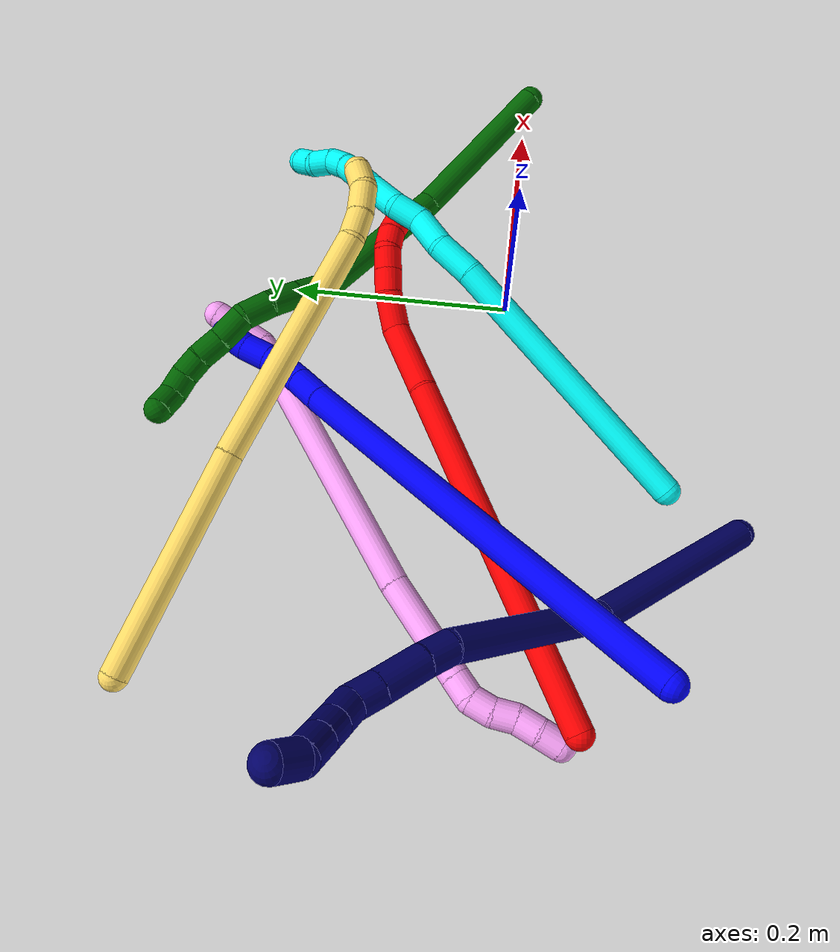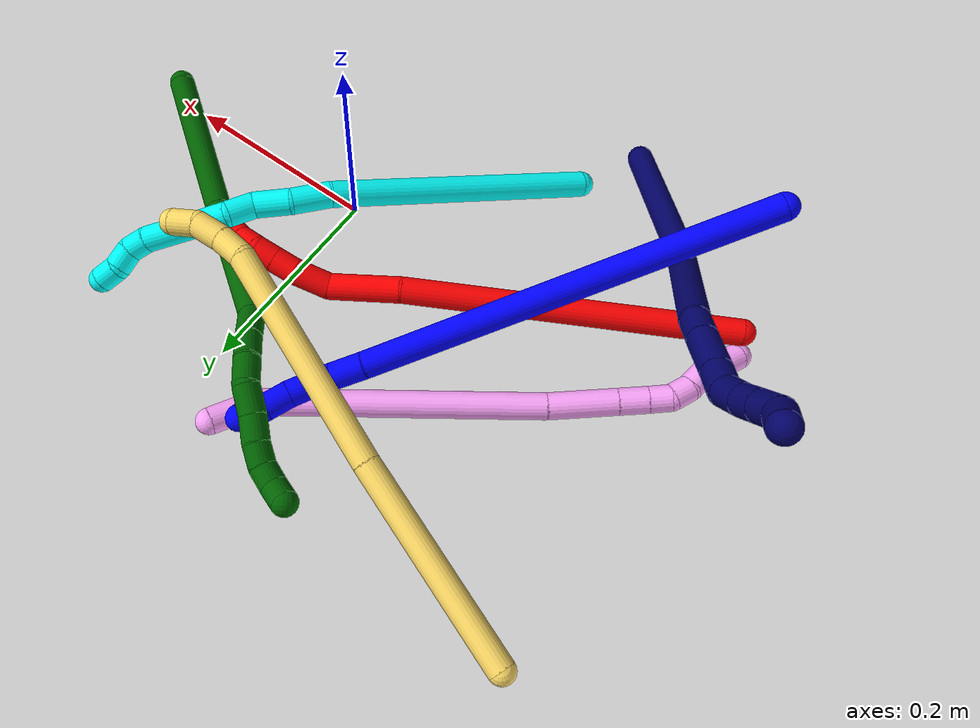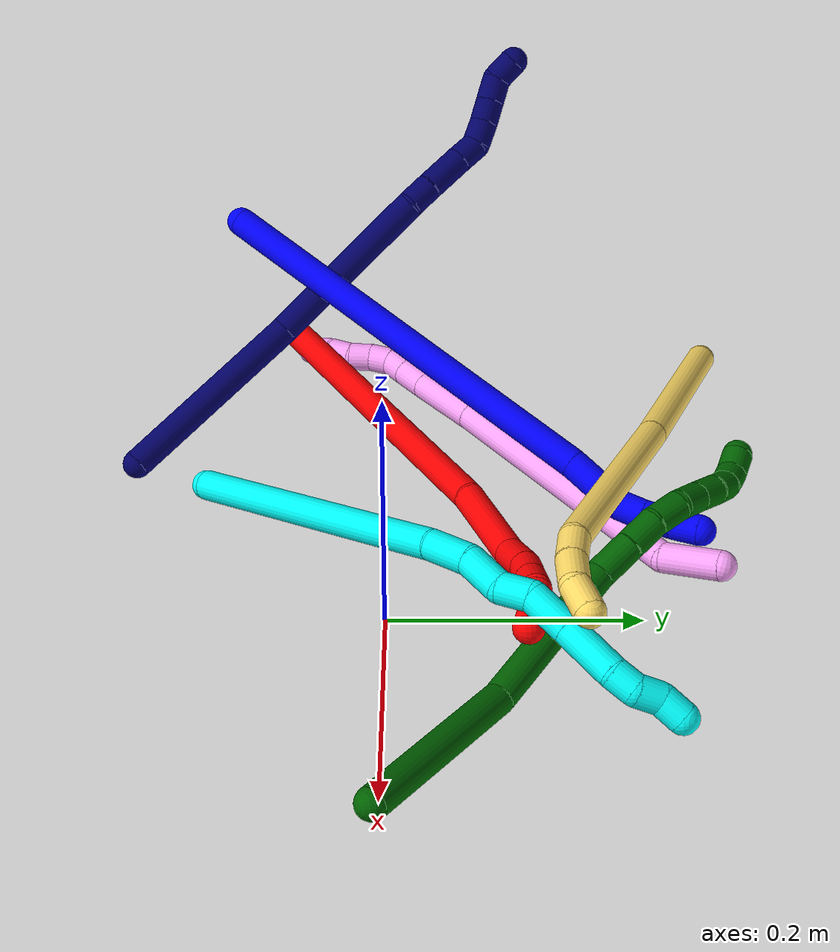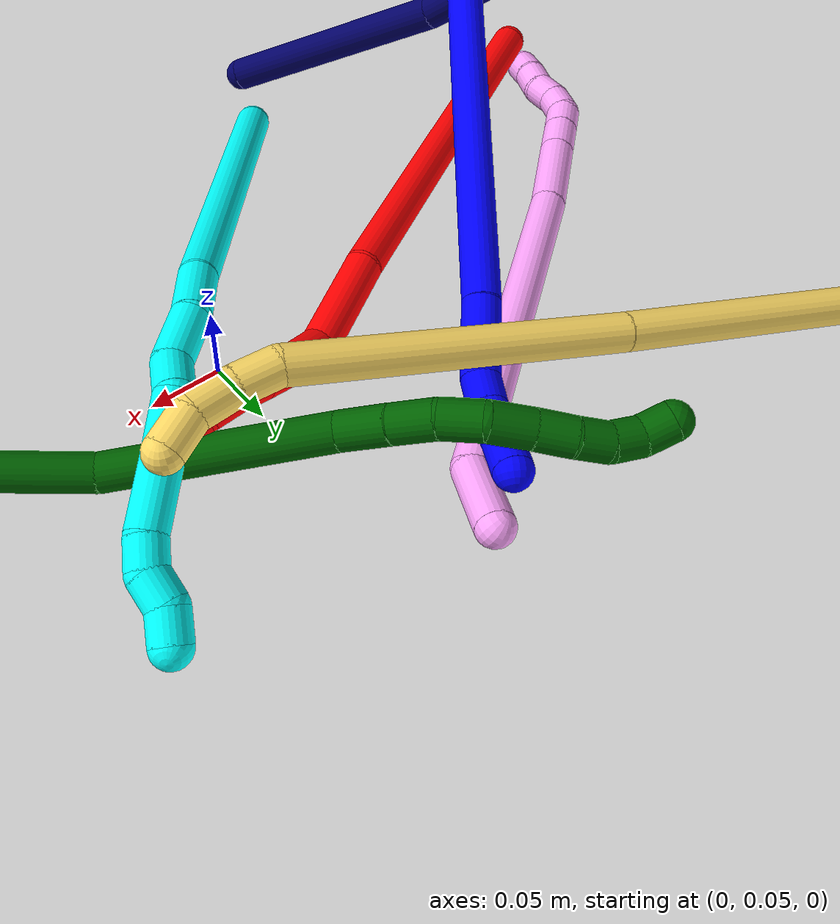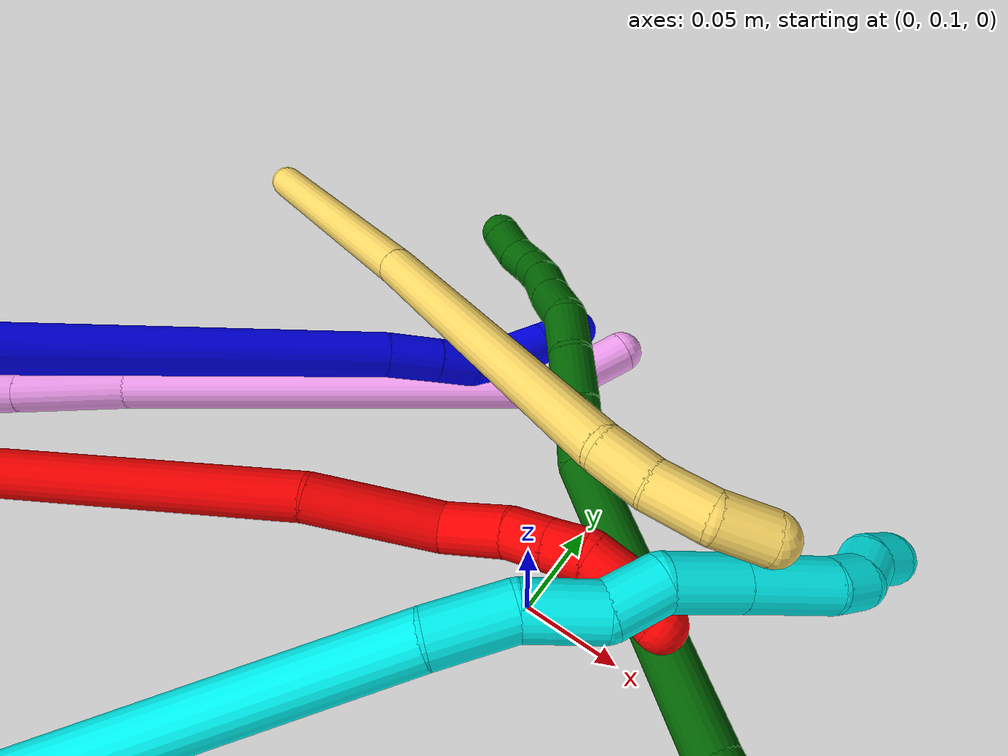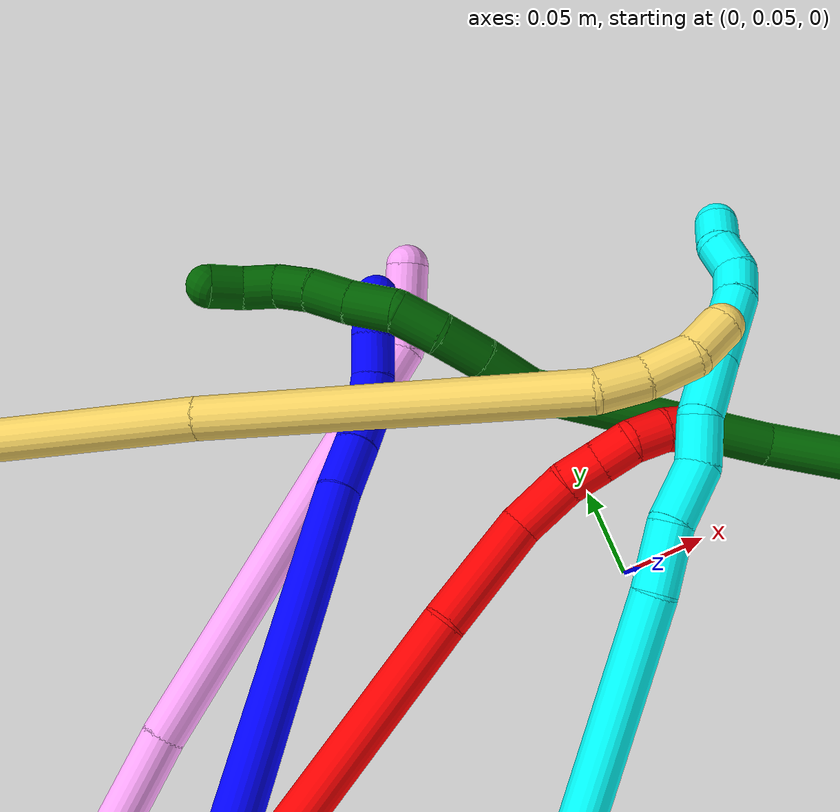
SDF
<sdf version="1.7">
 <world name="default">
  <plugin name="TubeGeneratorPlugin" filename="libtube_generator_plugin.so"/>
  <model name="photoneo_s_sensor">
   <static>1</static>
   <pose>0 0 2 1.57079 1.57079 3.14159</pose>
   <link name="link">
    <inertial><mass>0.1</mass></inertial>
    <sensor name="sensor" type="depth">
     <update_rate>30</update_rate>
     <camera>
      <horizontal_fov>1.22</horizontal_fov>
      <image><width>1920</width><height>1200</height><format>B8G8R8</format></image>
      <clip><near>0.1</near><far>4</far></clip>
      <depth_camera><output>points</output></depth_camera>
     </camera>
     <plugin name="camera_plugin" filename="libgazebo_ros_depth_camera.so">
      <baseline>0.2</baseline>
      <alwaysOn>1</alwaysOn>
      <updateRate>0.0</updateRate>
      <cameraName>camera_ir</cameraName>
      <imageTopicName>/camera/color/image_raw</imageTopicName>
      <cameraInfoTopicName>/camera/color/camera_info</cameraInfoTopicName>
      <depthImageTopicName>/camera/depth/image_raw</depthImageTopicName>
      <depthImageCameraInfoTopicName>/camera/depth/camera_info</depthImageCameraInfoTopicName>
      <pointCloudTopicName>/camera/depth/points</pointCloudTopicName>
      <frameName>fr_optical</frameName>
      <pointCloudCutoff>0.1</pointCloudCutoff>
      <pointCloudCutoffMax>2.0</pointCloudCutoffMax>
      <distortionK1>0</distortionK1>
      <distortionK2>0</distortionK2>
      <distortionK3>0</distortionK3>
      <distortionT1>0</distortionT1>
      <distortionT2>0</distortionT2>
      <CxPrime>0</CxPrime>
      <Cx>0</Cx>
      <Cy>0</Cy>
      <focalLength>0</focalLength>
      <hackBaseline>0</hackBaseline>
     </plugin>
    </sensor>
   </link>
  </model>
  <gravity>0 0 -9.8</gravity>
  <magnetic_field>6e-06 2.3e-05 -4.2e-05</magnetic_field>
  <atmosphere type="adiabatic"/>
  <physics name="default_physics" default="0" type="ode">
   <max_step_size>0.003</max_step_size>
   <real_time_factor>1</real_time_factor>
   <real_time_update_rate>1000</real_time_update_rate>
   <max_contacts>10000</max_contacts>
   <ode>
    <solver>
     <type>quick</type>
     <iters>100</iters>
     <sor>1.3</sor>
     <use_dynamic_moi_rescaling>0</use_dynamic_moi_rescaling>
    </solver>
    <constraints>
     <contact_max_correcting_vel>0</contact_max_correcting_vel>
     <contact_surface_layer>0.001</contact_surface_layer>
     <cfm>0</cfm>
     <erp>0.2</erp>
    </constraints>
   </ode>
  </physics>
  <scene><ambient>0.4 0.4 0.4 1</ambient><background>0.7 0.7 0.7 1</background><shadows>0</shadows></scene>
  <audio><device>default</device></audio>
  <spherical_coordinates>
   <surface_model>EARTH_WGS84</surface_model>
   <latitude_deg>0</latitude_deg>
   <longitude_deg>0</longitude_deg>
   <elevation>0</elevation>
   <heading_deg>0</heading_deg>
  </spherical_coordinates>
  <model name="bin">
   <static>1</static>
   <link name="bottom">
    <collision name="collision-bottom">
     <pose>0 0 -0.01 0 -0 0</pose>
     <geometry><box><size>0.8 0.6 0.02</size></box></geometry>
     <surface>
      <friction><ode><mu>100</mu><mu2>100</mu2></ode></friction>
      <contact><collide_bitmask>65535</collide_bitmask></contact>
     </surface>
    </collision>
   </link>
   <link name="west_wall">
    <collision name="collision-west_wall">
     <pose>-0.41 0 0.1 0 -0 0</pose>
     <geometry><box><size>0.02 0.6 0.2</size></box></geometry>
     <surface>
      <friction><ode><mu>100</mu><mu2>100</mu2></ode></friction>
      <contact><collide_bitmask>65535</collide_bitmask></contact>
     </surface>
    </collision>
   </link>
   <link name="east_wall">
    <collision name="collision-east_wall">
     <pose>0.41 0 0.1 0 -0 0</pose>
     <geometry><box><size>0.02 0.6 0.2</size></box></geometry>
     <surface>
      <friction><ode><mu>100</mu><mu2>100</mu2></ode></friction>
      <contact><collide_bitmask>65535</collide_bitmask></contact>
     </surface>
    </collision>
   </link>
   <link name="south_wall">
    <collision name="collision-south_wall">
     <pose>0 -0.31 0.1 0 -0 0</pose>
     <geometry><box><size>0.8 0.02 0.2</size></box></geometry>
     <surface>
      <friction><ode><mu>100</mu><mu2>100</mu2></ode></friction>
      <contact><collide_bitmask>65535</collide_bitmask></contact>
     </surface>
    </collision>
   </link>
   <link name="north_wall">
    <collision name="collision-north_wall">
     <pose>0 0.31 0.1 0 -0 0</pose>
     <geometry><box><size>0.8 0.02 0.2</size></box></geometry>
     <surface>
      <friction><ode><mu>100</mu><mu2>100</mu2></ode></friction>
      <contact><collide_bitmask>65535</collide_bitmask></contact>
     </surface>
    </collision>
   </link>
  </model>
  <model name="1">
   <static>0</static>
   <link name="1">
    <collision name="collision-cylinder-e_1_1_4">
     <pose>0.001342 0.022761 -0.187699 -3.02092 0.0071 -0.117398</pose>
     <geometry><cylinder><radius>0.0125</radius><length>0.378158</length></cylinder></geometry>
     <surface>
      <friction><ode><mu>1.16</mu><mu2>1.16</mu2><slip1>0</slip1><slip2>0</slip2></ode></friction>
      <contact><ode><kp>1e+06</kp><kd>1</kd><max_vel>0</max_vel><min_depth>0.001</min_depth></ode></contact>
     </surface>
    </collision>
    <visual name="visual-cylinder-e_1_1_4">
     <pose>0.001342 0.022761 -0.187699 -3.02092 0.0071 -0.117398</pose>
     <geometry><cylinder><radius>0.0125</radius><length>0.378158</length></cylinder></geometry>
     <material><ambient>0 0 1 1</ambient></material>
    </visual>
    <collision name="collision-cylinder-e_2_4_5">
     <pose>0.004165 0.047129 -0.390256 -3.03385 0.098694 -1.48306</pose>
     <geometry><cylinder><radius>0.0125</radius><length>0.030034</length></cylinder></geometry>
     <surface>
      <friction><ode><mu>1.16</mu><mu2>1.16</mu2><slip1>0</slip1><slip2>0</slip2></ode></friction>
      <contact><ode><kp>1e+06</kp><kd>1</kd><max_vel>0</max_vel><min_depth>0.001</min_depth></ode></contact>
     </surface>
    </collision>
    <visual name="visual-cylinder-e_2_4_5">
     <pose>0.004165 0.047129 -0.390256 -3.03385 0.098694 -1.48306</pose>
     <geometry><cylinder><radius>0.0125</radius><length>0.030034</length></cylinder></geometry>
     <material><ambient>0 0 1 1</ambient></material>
    </visual>
    <collision name="collision-cylinder-e_3_5_6">
     <pose>0.006787 0.049477 -0.415746 -3.07197 0.106773 -1.98647</pose>
     <geometry><cylinder><radius>0.0125</radius><length>0.02144</length></cylinder></geometry>
     <surface>
      <friction><ode><mu>1.16</mu><mu2>1.16</mu2><slip1>0</slip1><slip2>0</slip2></ode></friction>
      <contact><ode><kp>1e+06</kp><kd>1</kd><max_vel>0</max_vel><min_depth>0.001</min_depth></ode></contact>
     </surface>
    </collision>
    <visual name="visual-cylinder-e_3_5_6">
     <pose>0.006787 0.049477 -0.415746 -3.07197 0.106773 -1.98647</pose>
     <geometry><cylinder><radius>0.0125</radius><length>0.02144</length></cylinder></geometry>
     <material><ambient>0 0 1 1</ambient></material>
    </visual>
    <collision name="collision-cylinder-e_4_6_7">
     <pose>0.005461 0.052015 -0.437085 -2.97534 -0.223591 1.86464</pose>
     <geometry><cylinder><radius>0.0125</radius><length>0.022265</length></cylinder></geometry>
     <surface>
      <friction><ode><mu>1.16</mu><mu2>1.16</mu2><slip1>0</slip1><slip2>0</slip2></ode></friction>
      <contact><ode><kp>1e+06</kp><kd>1</kd><max_vel>0</max_vel><min_depth>0.001</min_depth></ode></contact>
     </surface>
    </collision>
    <visual name="visual-cylinder-e_4_6_7">
     <pose>0.005461 0.052015 -0.437085 -2.97534 -0.223591 1.86464</pose>
     <geometry><cylinder><radius>0.0125</radius><length>0.022265</length></cylinder></geometry>
     <material><ambient>0 0 1 1</ambient></material>
    </visual>
    <collision name="collision-cylinder-e_5_7_8">
     <pose>-0.000926 0.054727 -0.459162 -3.06129 -0.33082 2.66929</pose>
     <geometry><cylinder><radius>0.0125</radius><length>0.024125</length></cylinder></geometry>
     <surface>
      <friction><ode><mu>1.16</mu><mu2>1.16</mu2><slip1>0</slip1><slip2>0</slip2></ode></friction>
      <contact><ode><kp>1e+06</kp><kd>1</kd><max_vel>0</max_vel><min_depth>0.001</min_depth></ode></contact>
     </surface>
    </collision>
    <visual name="visual-cylinder-e_5_7_8">
     <pose>-0.000926 0.054727 -0.459162 -3.06129 -0.33082 2.66929</pose>
     <geometry><cylinder><radius>0.0125</radius><length>0.024125</length></cylinder></geometry>
     <material><ambient>0 0 1 1</ambient></material>
    </visual>
    <collision name="collision-cylinder-e_6_8_2">
     <pose>-0.009077 0.058403 -0.481406 -2.89285 -0.36087 1.93996</pose>
     <geometry><cylinder><radius>0.0125</radius><length>0.023978</length></cylinder></geometry>
     <surface>
      <friction><ode><mu>1.16</mu><mu2>1.16</mu2><slip1>0</slip1><slip2>0</slip2></ode></friction>
      <contact><ode><kp>1e+06</kp><kd>1</kd><max_vel>0</max_vel><min_depth>0.001</min_depth></ode></contact>
     </surface>
    </collision>
    <visual name="visual-cylinder-e_6_8_2">
     <pose>-0.009077 0.058403 -0.481406 -2.89285 -0.36087 1.93996</pose>
     <geometry><cylinder><radius>0.0125</radius><length>0.023978</length></cylinder></geometry>
     <material><ambient>0 0 1 1</ambient></material>
    </visual>
    <collision name="collision-sphere-2">
     <pose>-0.01331 0.061165 -0.492277 0 -0 0</pose>
     <geometry><sphere><radius>0.0125</radius></sphere></geometry>
     <surface>
      <friction><ode><mu>1.16</mu><mu2>1.16</mu2><slip1>0</slip1><slip2>0</slip2></ode></friction>
      <contact><ode><kp>1e+06</kp><kd>1</kd><max_vel>0</max_vel><min_depth>0.001</min_depth></ode></contact>
     </surface>
    </collision>
    <visual name="visual-sphere-2">
     <pose>-0.01331 0.061165 -0.492277 0 -0 0</pose>
     <geometry><sphere><radius>0.0125</radius></sphere></geometry>
     <material><ambient>0 0 1 1</ambient></material>
    </visual>
    <collision name="collision-sphere-4">
     <pose>0.002685 0.045522 -0.375398 0 -0 0</pose>
     <geometry><sphere><radius>0.0125</radius></sphere></geometry>
     <surface>
      <friction><ode><mu>1.16</mu><mu2>1.16</mu2><slip1>0</slip1><slip2>0</slip2></ode></friction>
      <contact><ode><kp>1e+06</kp><kd>1</kd><max_vel>0</max_vel><min_depth>0.001</min_depth></ode></contact>
     </surface>
    </collision>
    <visual name="visual-sphere-4">
     <pose>0.002685 0.045522 -0.375398 0 -0 0</pose>
     <geometry><sphere><radius>0.0125</radius></sphere></geometry>
     <material><ambient>0 0 1 1</ambient></material>
    </visual>
    <collision name="collision-sphere-1">
     <geometry><sphere><radius>0.0125</radius></sphere></geometry>
     <surface>
      <friction><ode><mu>1.16</mu><mu2>1.16</mu2><slip1>0</slip1><slip2>0</slip2></ode></friction>
      <contact><ode><kp>1e+06</kp><kd>1</kd><max_vel>0</max_vel><min_depth>0.001</min_depth></ode></contact>
     </surface>
    </collision>
    <visual name="visual-sphere-1">
     <geometry><sphere><radius>0.0125</radius></sphere></geometry>
     <material><ambient>0 0 1 1</ambient></material>
    </visual>
    <collision name="collision-sphere-8">
     <pose>-0.004844 0.055642 -0.470534 0 -0 0</pose>
     <geometry><sphere><radius>0.0125</radius></sphere></geometry>
     <surface>
      <friction><ode><mu>1.16</mu><mu2>1.16</mu2><slip1>0</slip1><slip2>0</slip2></ode></friction>
      <contact><ode><kp>1e+06</kp><kd>1</kd><max_vel>0</max_vel><min_depth>0.001</min_depth></ode></contact>
     </surface>
    </collision>
    <visual name="visual-sphere-8">
     <pose>-0.004844 0.055642 -0.470534 0 -0 0</pose>
     <geometry><sphere><radius>0.0125</radius></sphere></geometry>
     <material><ambient>0 0 1 1</ambient></material>
    </visual>
    <collision name="collision-sphere-5">
     <pose>0.005644 0.048736 -0.405113 0 -0 0</pose>
     <geometry><sphere><radius>0.0125</radius></sphere></geometry>
     <surface>
      <friction><ode><mu>1.16</mu><mu2>1.16</mu2><slip1>0</slip1><slip2>0</slip2></ode></friction>
      <contact><ode><kp>1e+06</kp><kd>1</kd><max_vel>0</max_vel><min_depth>0.001</min_depth></ode></contact>
     </surface>
    </collision>
    <visual name="visual-sphere-5">
     <pose>0.005644 0.048736 -0.405113 0 -0 0</pose>
     <geometry><sphere><radius>0.0125</radius></sphere></geometry>
     <material><ambient>0 0 1 1</ambient></material>
    </visual>
    <collision name="collision-sphere-6">
     <pose>0.007929 0.050219 -0.426379 0 -0 0</pose>
     <geometry><sphere><radius>0.0125</radius></sphere></geometry>
     <surface>
      <friction><ode><mu>1.16</mu><mu2>1.16</mu2><slip1>0</slip1><slip2>0</slip2></ode></friction>
      <contact><ode><kp>1e+06</kp><kd>1</kd><max_vel>0</max_vel><min_depth>0.001</min_depth></ode></contact>
     </surface>
    </collision>
    <visual name="visual-sphere-6">
     <pose>0.007929 0.050219 -0.426379 0 -0 0</pose>
     <geometry><sphere><radius>0.0125</radius></sphere></geometry>
     <material><ambient>0 0 1 1</ambient></material>
    </visual>
    <collision name="collision-sphere-7">
     <pose>0.002992 0.053812 -0.447791 0 -0 0</pose>
     <geometry><sphere><radius>0.0125</radius></sphere></geometry>
     <surface>
      <friction><ode><mu>1.16</mu><mu2>1.16</mu2><slip1>0</slip1><slip2>0</slip2></ode></friction>
      <contact><ode><kp>1e+06</kp><kd>1</kd><max_vel>0</max_vel><min_depth>0.001</min_depth></ode></contact>
     </surface>
    </collision>
    <visual name="visual-sphere-7">
     <pose>0.002992 0.053812 -0.447791 0 -0 0</pose>
     <geometry><sphere><radius>0.0125</radius></sphere></geometry>
     <material><ambient>0 0 1 1</ambient></material>
    </visual>
    <inertial>
     <pose>0.00132 0.029925 -0.247933 0 -0 0</pose>
     <mass>0.5</mass>
     <inertia>
      <ixx>0.003956</ixx>
      <ixy>0</ixy>
      <ixz>0</ixz>
      <iyy>-0.004979</iyy>
      <iyz>0</iyz>
      <izz>-0.000615</izz>
     </inertia>
    </inertial>
   </link>
   <pose>-0.358706 -0.133777 0.162223 1.0774 0.70933 -0.912112</pose>
  </model>
  <model name="2">
   <static>0</static>
   <link name="2">
    <collision name="collision-cylinder-e_1_1_4">
     <pose>0.121626 0.0782 -0.059984 -2.22512 0.889791 -1.53683</pose>
     <geometry><cylinder><radius>0.0125</radius><length>0.313089</length></cylinder></geometry>
     <surface>
      <friction><ode><mu>1.16</mu><mu2>1.16</mu2><slip1>0</slip1><slip2>0</slip2></ode></friction>
      <contact><ode><kp>1e+06</kp><kd>1</kd><max_vel>0</max_vel><min_depth>0.001</min_depth></ode></contact>
     </surface>
    </collision>
    <visual name="visual-cylinder-e_1_1_4">
     <pose>0.121626 0.0782 -0.059984 -2.22512 0.889791 -1.53683</pose>
     <geometry><cylinder><radius>0.0125</radius><length>0.313089</length></cylinder></geometry>
     <material><ambient>1 0 0 1</ambient></material>
    </visual>
    <collision name="collision-cylinder-e_2_4_5">
     <pose>0.273727 0.167955 -0.132087 -2.38006 1.06839 -1.95178</pose>
     <geometry><cylinder><radius>0.0125</radius><length>0.069544</length></cylinder></geometry>
     <surface>
      <friction><ode><mu>1.16</mu><mu2>1.16</mu2><slip1>0</slip1><slip2>0</slip2></ode></friction>
      <contact><ode><kp>1e+06</kp><kd>1</kd><max_vel>0</max_vel><min_depth>0.001</min_depth></ode></contact>
     </surface>
    </collision>
    <visual name="visual-cylinder-e_2_4_5">
     <pose>0.273727 0.167955 -0.132087 -2.38006 1.06839 -1.95178</pose>
     <geometry><cylinder><radius>0.0125</radius><length>0.069544</length></cylinder></geometry>
     <material><ambient>1 0 0 1</ambient></material>
    </visual>
    <collision name="collision-cylinder-e_3_5_6">
     <pose>0.315531 0.192477 -0.147828 -1.84319 0.699446 -0.895943</pose>
     <geometry><cylinder><radius>0.0125</radius><length>0.035194</length></cylinder></geometry>
     <surface>
      <friction><ode><mu>1.16</mu><mu2>1.16</mu2><slip1>0</slip1><slip2>0</slip2></ode></friction>
      <contact><ode><kp>1e+06</kp><kd>1</kd><max_vel>0</max_vel><min_depth>0.001</min_depth></ode></contact>
     </surface>
    </collision>
    <visual name="visual-cylinder-e_3_5_6">
     <pose>0.315531 0.192477 -0.147828 -1.84319 0.699446 -0.895943</pose>
     <geometry><cylinder><radius>0.0125</radius><length>0.035194</length></cylinder></geometry>
     <material><ambient>1 0 0 1</ambient></material>
    </visual>
    <collision name="collision-cylinder-e_4_6_7">
     <pose>0.334757 0.212996 -0.151751 -1.6105 0.807529 -0.836619</pose>
     <geometry><cylinder><radius>0.0125</radius><length>0.021859</length></cylinder></geometry>
     <surface>
      <friction><ode><mu>1.16</mu><mu2>1.16</mu2><slip1>0</slip1><slip2>0</slip2></ode></friction>
      <contact><ode><kp>1e+06</kp><kd>1</kd><max_vel>0</max_vel><min_depth>0.001</min_depth></ode></contact>
     </surface>
    </collision>
    <visual name="visual-cylinder-e_4_6_7">
     <pose>0.334757 0.212996 -0.151751 -1.6105 0.807529 -0.836619</pose>
     <geometry><cylinder><radius>0.0125</radius><length>0.021859</length></cylinder></geometry>
     <material><ambient>1 0 0 1</ambient></material>
    </visual>
    <collision name="collision-cylinder-e_5_7_8">
     <pose>0.349725 0.227728 -0.152352 -1.61273 0.777082 -0.806937</pose>
     <geometry><cylinder><radius>0.0125</radius><length>0.020168</length></cylinder></geometry>
     <surface>
      <friction><ode><mu>1.16</mu><mu2>1.16</mu2><slip1>0</slip1><slip2>0</slip2></ode></friction>
      <contact><ode><kp>1e+06</kp><kd>1</kd><max_vel>0</max_vel><min_depth>0.001</min_depth></ode></contact>
     </surface>
    </collision>
    <visual name="visual-cylinder-e_5_7_8">
     <pose>0.349725 0.227728 -0.152352 -1.61273 0.777082 -0.806937</pose>
     <geometry><cylinder><radius>0.0125</radius><length>0.020168</length></cylinder></geometry>
     <material><ambient>1 0 0 1</ambient></material>
    </visual>
    <collision name="collision-cylinder-e_6_8_9">
     <pose>0.365901 0.238875 -0.151025 -1.18087 1.13088 -0.804202</pose>
     <geometry><cylinder><radius>0.0125</radius><length>0.020125</length></cylinder></geometry>
     <surface>
      <friction><ode><mu>1.16</mu><mu2>1.16</mu2><slip1>0</slip1><slip2>0</slip2></ode></friction>
      <contact><ode><kp>1e+06</kp><kd>1</kd><max_vel>0</max_vel><min_depth>0.001</min_depth></ode></contact>
     </surface>
    </collision>
    <visual name="visual-cylinder-e_6_8_9">
     <pose>0.365901 0.238875 -0.151025 -1.18087 1.13088 -0.804202</pose>
     <geometry><cylinder><radius>0.0125</radius><length>0.020125</length></cylinder></geometry>
     <material><ambient>1 0 0 1</ambient></material>
    </visual>
    <collision name="collision-cylinder-e_7_9_2">
     <pose>0.383669 0.246072 -0.145564 -0.70088 1.04617 -0.415492</pose>
     <geometry><cylinder><radius>0.0125</radius><length>0.020021</length></cylinder></geometry>
     <surface>
      <friction><ode><mu>1.16</mu><mu2>1.16</mu2><slip1>0</slip1><slip2>0</slip2></ode></friction>
      <contact><ode><kp>1e+06</kp><kd>1</kd><max_vel>0</max_vel><min_depth>0.001</min_depth></ode></contact>
     </surface>
    </collision>
    <visual name="visual-cylinder-e_7_9_2">
     <pose>0.383669 0.246072 -0.145564 -0.70088 1.04617 -0.415492</pose>
     <geometry><cylinder><radius>0.0125</radius><length>0.020021</length></cylinder></geometry>
     <material><ambient>1 0 0 1</ambient></material>
    </visual>
    <collision name="collision-sphere-2">
     <pose>0.392333 0.249306 -0.141731 0 -0 0</pose>
     <geometry><sphere><radius>0.0125</radius></sphere></geometry>
     <surface>
      <friction><ode><mu>1.16</mu><mu2>1.16</mu2><slip1>0</slip1><slip2>0</slip2></ode></friction>
      <contact><ode><kp>1e+06</kp><kd>1</kd><max_vel>0</max_vel><min_depth>0.001</min_depth></ode></contact>
     </surface>
    </collision>
    <visual name="visual-sphere-2">
     <pose>0.392333 0.249306 -0.141731 0 -0 0</pose>
     <geometry><sphere><radius>0.0125</radius></sphere></geometry>
     <material><ambient>1 0 0 1</ambient></material>
    </visual>
    <collision name="collision-sphere-9">
     <pose>0.375005 0.242838 -0.149396 0 -0 0</pose>
     <geometry><sphere><radius>0.0125</radius></sphere></geometry>
     <surface>
      <friction><ode><mu>1.16</mu><mu2>1.16</mu2><slip1>0</slip1><slip2>0</slip2></ode></friction>
      <contact><ode><kp>1e+06</kp><kd>1</kd><max_vel>0</max_vel><min_depth>0.001</min_depth></ode></contact>
     </surface>
    </collision>
    <visual name="visual-sphere-9">
     <pose>0.375005 0.242838 -0.149396 0 -0 0</pose>
     <geometry><sphere><radius>0.0125</radius></sphere></geometry>
     <material><ambient>1 0 0 1</ambient></material>
    </visual>
    <collision name="collision-sphere-4">
     <pose>0.243252 0.156401 -0.119968 0 -0 0</pose>
     <geometry><sphere><radius>0.0125</radius></sphere></geometry>
     <surface>
      <friction><ode><mu>1.16</mu><mu2>1.16</mu2><slip1>0</slip1><slip2>0</slip2></ode></friction>
      <contact><ode><kp>1e+06</kp><kd>1</kd><max_vel>0</max_vel><min_depth>0.001</min_depth></ode></contact>
     </surface>
    </collision>
    <visual name="visual-sphere-4">
     <pose>0.243252 0.156401 -0.119968 0 -0 0</pose>
     <geometry><sphere><radius>0.0125</radius></sphere></geometry>
     <material><ambient>1 0 0 1</ambient></material>
    </visual>
    <collision name="collision-sphere-1">
     <geometry><sphere><radius>0.0125</radius></sphere></geometry>
     <surface>
      <friction><ode><mu>1.16</mu><mu2>1.16</mu2><slip1>0</slip1><slip2>0</slip2></ode></friction>
      <contact><ode><kp>1e+06</kp><kd>1</kd><max_vel>0</max_vel><min_depth>0.001</min_depth></ode></contact>
     </surface>
    </collision>
    <visual name="visual-sphere-1">
     <geometry><sphere><radius>0.0125</radius></sphere></geometry>
     <material><ambient>1 0 0 1</ambient></material>
    </visual>
    <collision name="collision-sphere-8">
     <pose>0.356796 0.234911 -0.152654 0 -0 0</pose>
     <geometry><sphere><radius>0.0125</radius></sphere></geometry>
     <surface>
      <friction><ode><mu>1.16</mu><mu2>1.16</mu2><slip1>0</slip1><slip2>0</slip2></ode></friction>
      <contact><ode><kp>1e+06</kp><kd>1</kd><max_vel>0</max_vel><min_depth>0.001</min_depth></ode></contact>
     </surface>
    </collision>
    <visual name="visual-sphere-8">
     <pose>0.356796 0.234911 -0.152654 0 -0 0</pose>
     <geometry><sphere><radius>0.0125</radius></sphere></geometry>
     <material><ambient>1 0 0 1</ambient></material>
    </visual>
    <collision name="collision-sphere-5">
     <pose>0.304202 0.179508 -0.144205 0 -0 0</pose>
     <geometry><sphere><radius>0.0125</radius></sphere></geometry>
     <surface>
      <friction><ode><mu>1.16</mu><mu2>1.16</mu2><slip1>0</slip1><slip2>0</slip2></ode></friction>
      <contact><ode><kp>1e+06</kp><kd>1</kd><max_vel>0</max_vel><min_depth>0.001</min_depth></ode></contact>
     </surface>
    </collision>
    <visual name="visual-sphere-5">
     <pose>0.304202 0.179508 -0.144205 0 -0 0</pose>
     <geometry><sphere><radius>0.0125</radius></sphere></geometry>
     <material><ambient>1 0 0 1</ambient></material>
    </visual>
    <collision name="collision-sphere-6">
     <pose>0.32686 0.205446 -0.151451 0 -0 0</pose>
     <geometry><sphere><radius>0.0125</radius></sphere></geometry>
     <surface>
      <friction><ode><mu>1.16</mu><mu2>1.16</mu2><slip1>0</slip1><slip2>0</slip2></ode></friction>
      <contact><ode><kp>1e+06</kp><kd>1</kd><max_vel>0</max_vel><min_depth>0.001</min_depth></ode></contact>
     </surface>
    </collision>
    <visual name="visual-sphere-6">
     <pose>0.32686 0.205446 -0.151451 0 -0 0</pose>
     <geometry><sphere><radius>0.0125</radius></sphere></geometry>
     <material><ambient>1 0 0 1</ambient></material>
    </visual>
    <collision name="collision-sphere-7">
     <pose>0.342655 0.220545 -0.152051 0 -0 0</pose>
     <geometry><sphere><radius>0.0125</radius></sphere></geometry>
     <surface>
      <friction><ode><mu>1.16</mu><mu2>1.16</mu2><slip1>0</slip1><slip2>0</slip2></ode></friction>
      <contact><ode><kp>1e+06</kp><kd>1</kd><max_vel>0</max_vel><min_depth>0.001</min_depth></ode></contact>
     </surface>
    </collision>
    <visual name="visual-sphere-7">
     <pose>0.342655 0.220545 -0.152051 0 -0 0</pose>
     <geometry><sphere><radius>0.0125</radius></sphere></geometry>
     <material><ambient>1 0 0 1</ambient></material>
    </visual>
    <inertial>
     <pose>0.195273 0.123841 -0.091024 0 -0 0</pose>
     <mass>0.5</mass>
     <inertia>
      <ixx>-0.001551</ixx>
      <ixy>0</ixy>
      <ixz>0</ixz>
      <iyy>-5.5e-05</iyy>
      <iyz>0</iyz>
      <izz>-0.003344</izz>
     </inertia>
    </inertial>
   </link>
   <pose>-0.38109 -0.088815 0.033182 1.58792 0.548737 0.129745</pose>
  </model>
  <model name="3">
   <static>0</static>
   <link name="3">
    <collision name="collision-cylinder-e_1_1_4">
     <pose>-0.000203 0.000655 0.128577 -0.005098 -0.001576 4e-06</pose>
     <geometry><cylinder><radius>0.0125</radius><length>0.257159</length></cylinder></geometry>
     <surface>
      <friction><ode><mu>1.16</mu><mu2>1.16</mu2><slip1>0</slip1><slip2>0</slip2></ode></friction>
      <contact><ode><kp>1e+06</kp><kd>1</kd><max_vel>0</max_vel><min_depth>0.001</min_depth></ode></contact>
     </surface>
    </collision>
    <visual name="visual-cylinder-e_1_1_4">
     <pose>-0.000203 0.000655 0.128577 -0.005098 -0.001576 4e-06</pose>
     <geometry><cylinder><radius>0.0125</radius><length>0.257159</length></cylinder></geometry>
     <material><ambient>0.003922 1 0.996078 1</ambient></material>
    </visual>
    <collision name="collision-cylinder-e_2_4_5">
     <pose>-0.002354 0.003815 0.275465 -0.135912 -0.105045 0.007156</pose>
     <geometry><cylinder><radius>0.0125</radius><length>0.037166</length></cylinder></geometry>
     <surface>
      <friction><ode><mu>1.16</mu><mu2>1.16</mu2><slip1>0</slip1><slip2>0</slip2></ode></friction>
      <contact><ode><kp>1e+06</kp><kd>1</kd><max_vel>0</max_vel><min_depth>0.001</min_depth></ode></contact>
     </surface>
    </collision>
    <visual name="visual-cylinder-e_2_4_5">
     <pose>-0.002354 0.003815 0.275465 -0.135912 -0.105045 0.007156</pose>
     <geometry><cylinder><radius>0.0125</radius><length>0.037166</length></cylinder></geometry>
     <material><ambient>0.003922 1 0.996078 1</ambient></material>
    </visual>
    <collision name="collision-cylinder-e_3_5_6">
     <pose>-0.003591 0.013414 0.310112 -0.409704 0.039905 -0.008292</pose>
     <geometry><cylinder><radius>0.0125</radius><length>0.035651</length></cylinder></geometry>
     <surface>
      <friction><ode><mu>1.16</mu><mu2>1.16</mu2><slip1>0</slip1><slip2>0</slip2></ode></friction>
      <contact><ode><kp>1e+06</kp><kd>1</kd><max_vel>0</max_vel><min_depth>0.001</min_depth></ode></contact>
     </surface>
    </collision>
    <visual name="visual-cylinder-e_3_5_6">
     <pose>-0.003591 0.013414 0.310112 -0.409704 0.039905 -0.008292</pose>
     <geometry><cylinder><radius>0.0125</radius><length>0.035651</length></cylinder></geometry>
     <material><ambient>0.003922 1 0.996078 1</ambient></material>
    </visual>
    <collision name="collision-cylinder-e_4_6_7">
     <pose>-0.006583 0.021422 0.339153 -0.071724 -0.282992 0.010221</pose>
     <geometry><cylinder><radius>0.0125</radius><length>0.026527</length></cylinder></geometry>
     <surface>
      <friction><ode><mu>1.16</mu><mu2>1.16</mu2><slip1>0</slip1><slip2>0</slip2></ode></friction>
      <contact><ode><kp>1e+06</kp><kd>1</kd><max_vel>0</max_vel><min_depth>0.001</min_depth></ode></contact>
     </surface>
    </collision>
    <visual name="visual-cylinder-e_4_6_7">
     <pose>-0.006583 0.021422 0.339153 -0.071724 -0.282992 0.010221</pose>
     <geometry><cylinder><radius>0.0125</radius><length>0.026527</length></cylinder></geometry>
     <material><ambient>0.003922 1 0.996078 1</ambient></material>
    </visual>
    <collision name="collision-cylinder-e_5_7_8">
     <pose>-0.012816 0.031401 0.367461 -0.526346 -0.13924 0.037571</pose>
     <geometry><cylinder><radius>0.0125</radius><length>0.036448</length></cylinder></geometry>
     <surface>
      <friction><ode><mu>1.16</mu><mu2>1.16</mu2><slip1>0</slip1><slip2>0</slip2></ode></friction>
      <contact><ode><kp>1e+06</kp><kd>1</kd><max_vel>0</max_vel><min_depth>0.001</min_depth></ode></contact>
     </surface>
    </collision>
    <visual name="visual-cylinder-e_5_7_8">
     <pose>-0.012816 0.031401 0.367461 -0.526346 -0.13924 0.037571</pose>
     <geometry><cylinder><radius>0.0125</radius><length>0.036448</length></cylinder></geometry>
     <material><ambient>0.003922 1 0.996078 1</ambient></material>
    </visual>
    <collision name="collision-cylinder-e_6_8_9">
     <pose>-0.018099 0.052151 0.402876 -0.532863 -0.119163 0.032558</pose>
     <geometry><cylinder><radius>0.0125</radius><length>0.046326</length></cylinder></geometry>
     <surface>
      <friction><ode><mu>1.16</mu><mu2>1.16</mu2><slip1>0</slip1><slip2>0</slip2></ode></friction>
      <contact><ode><kp>1e+06</kp><kd>1</kd><max_vel>0</max_vel><min_depth>0.001</min_depth></ode></contact>
     </surface>
    </collision>
    <visual name="visual-cylinder-e_6_8_9">
     <pose>-0.018099 0.052151 0.402876 -0.532863 -0.119163 0.032558</pose>
     <geometry><cylinder><radius>0.0125</radius><length>0.046326</length></cylinder></geometry>
     <material><ambient>0.003922 1 0.996078 1</ambient></material>
    </visual>
    <collision name="collision-cylinder-e_7_9_10">
     <pose>-0.024368 0.068853 0.430592 -0.565568 -0.359056 0.105369</pose>
     <geometry><cylinder><radius>0.0125</radius><length>0.020004</length></cylinder></geometry>
     <surface>
      <friction><ode><mu>1.16</mu><mu2>1.16</mu2><slip1>0</slip1><slip2>0</slip2></ode></friction>
      <contact><ode><kp>1e+06</kp><kd>1</kd><max_vel>0</max_vel><min_depth>0.001</min_depth></ode></contact>
     </surface>
    </collision>
    <visual name="visual-cylinder-e_7_9_10">
     <pose>-0.024368 0.068853 0.430592 -0.565568 -0.359056 0.105369</pose>
     <geometry><cylinder><radius>0.0125</radius><length>0.020004</length></cylinder></geometry>
     <material><ambient>0.003922 1 0.996078 1</ambient></material>
    </visual>
    <collision name="collision-cylinder-e_8_10_11">
     <pose>-0.035477 0.07663 0.44474 -0.41619 -0.838821 0.187737</pose>
     <geometry><cylinder><radius>0.0125</radius><length>0.020421</length></cylinder></geometry>
     <surface>
      <friction><ode><mu>1.16</mu><mu2>1.16</mu2><slip1>0</slip1><slip2>0</slip2></ode></friction>
      <contact><ode><kp>1e+06</kp><kd>1</kd><max_vel>0</max_vel><min_depth>0.001</min_depth></ode></contact>
     </surface>
    </collision>
    <visual name="visual-cylinder-e_8_10_11">
     <pose>-0.035477 0.07663 0.44474 -0.41619 -0.838821 0.187737</pose>
     <geometry><cylinder><radius>0.0125</radius><length>0.020421</length></cylinder></geometry>
     <material><ambient>0.003922 1 0.996078 1</ambient></material>
    </visual>
    <collision name="collision-cylinder-e_9_11_2">
     <pose>-0.047243 0.085187 0.458192 -0.677226 -0.423421 0.1511</pose>
     <geometry><cylinder><radius>0.0125</radius><length>0.020298</length></cylinder></geometry>
     <surface>
      <friction><ode><mu>1.16</mu><mu2>1.16</mu2><slip1>0</slip1><slip2>0</slip2></ode></friction>
      <contact><ode><kp>1e+06</kp><kd>1</kd><max_vel>0</max_vel><min_depth>0.001</min_depth></ode></contact>
     </surface>
    </collision>
    <visual name="visual-cylinder-e_9_11_2">
     <pose>-0.047243 0.085187 0.458192 -0.677226 -0.423421 0.1511</pose>
     <geometry><cylinder><radius>0.0125</radius><length>0.020298</length></cylinder></geometry>
     <material><ambient>0.003922 1 0.996078 1</ambient></material>
    </visual>
    <collision name="collision-sphere-2">
     <pose>-0.051413 0.090985 0.465403 0 -0 0</pose>
     <geometry><sphere><radius>0.0125</radius></sphere></geometry>
     <surface>
      <friction><ode><mu>1.16</mu><mu2>1.16</mu2><slip1>0</slip1><slip2>0</slip2></ode></friction>
      <contact><ode><kp>1e+06</kp><kd>1</kd><max_vel>0</max_vel><min_depth>0.001</min_depth></ode></contact>
     </surface>
    </collision>
    <visual name="visual-sphere-2">
     <pose>-0.051413 0.090985 0.465403 0 -0 0</pose>
     <geometry><sphere><radius>0.0125</radius></sphere></geometry>
     <material><ambient>0.003922 1 0.996078 1</ambient></material>
    </visual>
    <collision name="collision-sphere-11">
     <pose>-0.043073 0.079389 0.450981 0 -0 0</pose>
     <geometry><sphere><radius>0.0125</radius></sphere></geometry>
     <surface>
      <friction><ode><mu>1.16</mu><mu2>1.16</mu2><slip1>0</slip1><slip2>0</slip2></ode></friction>
      <contact><ode><kp>1e+06</kp><kd>1</kd><max_vel>0</max_vel><min_depth>0.001</min_depth></ode></contact>
     </surface>
    </collision>
    <visual name="visual-sphere-11">
     <pose>-0.043073 0.079389 0.450981 0 -0 0</pose>
     <geometry><sphere><radius>0.0125</radius></sphere></geometry>
     <material><ambient>0.003922 1 0.996078 1</ambient></material>
    </visual>
    <collision name="collision-sphere-10">
     <pose>-0.027882 0.073871 0.438498 0 -0 0</pose>
     <geometry><sphere><radius>0.0125</radius></sphere></geometry>
     <surface>
      <friction><ode><mu>1.16</mu><mu2>1.16</mu2><slip1>0</slip1><slip2>0</slip2></ode></friction>
      <contact><ode><kp>1e+06</kp><kd>1</kd><max_vel>0</max_vel><min_depth>0.001</min_depth></ode></contact>
     </surface>
    </collision>
    <visual name="visual-sphere-10">
     <pose>-0.027882 0.073871 0.438498 0 -0 0</pose>
     <geometry><sphere><radius>0.0125</radius></sphere></geometry>
     <material><ambient>0.003922 1 0.996078 1</ambient></material>
    </visual>
    <collision name="collision-sphere-9">
     <pose>-0.020853 0.063835 0.422686 0 -0 0</pose>
     <geometry><sphere><radius>0.0125</radius></sphere></geometry>
     <surface>
      <friction><ode><mu>1.16</mu><mu2>1.16</mu2><slip1>0</slip1><slip2>0</slip2></ode></friction>
      <contact><ode><kp>1e+06</kp><kd>1</kd><max_vel>0</max_vel><min_depth>0.001</min_depth></ode></contact>
     </surface>
    </collision>
    <visual name="visual-sphere-9">
     <pose>-0.020853 0.063835 0.422686 0 -0 0</pose>
     <geometry><sphere><radius>0.0125</radius></sphere></geometry>
     <material><ambient>0.003922 1 0.996078 1</ambient></material>
    </visual>
    <collision name="collision-sphere-4">
     <pose>-0.000405 0.001311 0.257155 0 -0 0</pose>
     <geometry><sphere><radius>0.0125</radius></sphere></geometry>
     <surface>
      <friction><ode><mu>1.16</mu><mu2>1.16</mu2><slip1>0</slip1><slip2>0</slip2></ode></friction>
      <contact><ode><kp>1e+06</kp><kd>1</kd><max_vel>0</max_vel><min_depth>0.001</min_depth></ode></contact>
     </surface>
    </collision>
    <visual name="visual-sphere-4">
     <pose>-0.000405 0.001311 0.257155 0 -0 0</pose>
     <geometry><sphere><radius>0.0125</radius></sphere></geometry>
     <material><ambient>0.003922 1 0.996078 1</ambient></material>
    </visual>
    <collision name="collision-sphere-1">
     <geometry><sphere><radius>0.0125</radius></sphere></geometry>
     <surface>
      <friction><ode><mu>1.16</mu><mu2>1.16</mu2><slip1>0</slip1><slip2>0</slip2></ode></friction>
      <contact><ode><kp>1e+06</kp><kd>1</kd><max_vel>0</max_vel><min_depth>0.001</min_depth></ode></contact>
     </surface>
    </collision>
    <visual name="visual-sphere-1">
     <geometry><sphere><radius>0.0125</radius></sphere></geometry>
     <material><ambient>0.003922 1 0.996078 1</ambient></material>
    </visual>
    <collision name="collision-sphere-8">
     <pose>-0.015346 0.040468 0.383066 0 -0 0</pose>
     <geometry><sphere><radius>0.0125</radius></sphere></geometry>
     <surface>
      <friction><ode><mu>1.16</mu><mu2>1.16</mu2><slip1>0</slip1><slip2>0</slip2></ode></friction>
      <contact><ode><kp>1e+06</kp><kd>1</kd><max_vel>0</max_vel><min_depth>0.001</min_depth></ode></contact>
     </surface>
    </collision>
    <visual name="visual-sphere-8">
     <pose>-0.015346 0.040468 0.383066 0 -0 0</pose>
     <geometry><sphere><radius>0.0125</radius></sphere></geometry>
     <material><ambient>0.003922 1 0.996078 1</ambient></material>
    </visual>
    <collision name="collision-sphere-5">
     <pose>-0.004302 0.006319 0.293775 0 -0 0</pose>
     <geometry><sphere><radius>0.0125</radius></sphere></geometry>
     <surface>
      <friction><ode><mu>1.16</mu><mu2>1.16</mu2><slip1>0</slip1><slip2>0</slip2></ode></friction>
      <contact><ode><kp>1e+06</kp><kd>1</kd><max_vel>0</max_vel><min_depth>0.001</min_depth></ode></contact>
     </surface>
    </collision>
    <visual name="visual-sphere-5">
     <pose>-0.004302 0.006319 0.293775 0 -0 0</pose>
     <geometry><sphere><radius>0.0125</radius></sphere></geometry>
     <material><ambient>0.003922 1 0.996078 1</ambient></material>
    </visual>
    <collision name="collision-sphere-6">
     <pose>-0.00288 0.020509 0.326449 0 -0 0</pose>
     <geometry><sphere><radius>0.0125</radius></sphere></geometry>
     <surface>
      <friction><ode><mu>1.16</mu><mu2>1.16</mu2><slip1>0</slip1><slip2>0</slip2></ode></friction>
      <contact><ode><kp>1e+06</kp><kd>1</kd><max_vel>0</max_vel><min_depth>0.001</min_depth></ode></contact>
     </surface>
    </collision>
    <visual name="visual-sphere-6">
     <pose>-0.00288 0.020509 0.326449 0 -0 0</pose>
     <geometry><sphere><radius>0.0125</radius></sphere></geometry>
     <material><ambient>0.003922 1 0.996078 1</ambient></material>
    </visual>
    <collision name="collision-sphere-7">
     <pose>-0.010287 0.022334 0.351856 0 -0 0</pose>
     <geometry><sphere><radius>0.0125</radius></sphere></geometry>
     <surface>
      <friction><ode><mu>1.16</mu><mu2>1.16</mu2><slip1>0</slip1><slip2>0</slip2></ode></friction>
      <contact><ode><kp>1e+06</kp><kd>1</kd><max_vel>0</max_vel><min_depth>0.001</min_depth></ode></contact>
     </surface>
    </collision>
    <visual name="visual-sphere-7">
     <pose>-0.010287 0.022334 0.351856 0 -0 0</pose>
     <geometry><sphere><radius>0.0125</radius></sphere></geometry>
     <material><ambient>0.003922 1 0.996078 1</ambient></material>
    </visual>
    <inertial>
     <pose>-0.007837 0.019177 0.244817 0 -0 0</pose>
     <mass>0.5</mass>
     <inertia>
      <ixx>0.001457</ixx>
      <ixy>0</ixy>
      <ixz>0</ixz>
      <iyy>0.001466</iyy>
      <iyz>0</iyz>
      <izz>2.4e-05</izz>
     </inertia>
    </inertial>
   </link>
   <pose>-0.166998 -0.154045 0.011495 -1.31811 -0.375974 -0.806908</pose>
  </model>
  <model name="4">
   <static>0</static>
   <link name="4">
    <collision name="collision-cylinder-e_1_1_4">
     <pose>-0.020145 -0.013862 0.004207 1.27617 -0.947354 -0.726522</pose>
     <geometry><cylinder><radius>0.0125</radius><length>0.049626</length></cylinder></geometry>
     <surface>
      <friction><ode><mu>1.16</mu><mu2>1.16</mu2><slip1>0</slip1><slip2>0</slip2></ode></friction>
      <contact><ode><kp>1e+06</kp><kd>1</kd><max_vel>0</max_vel><min_depth>0.001</min_depth></ode></contact>
     </surface>
    </collision>
    <visual name="visual-cylinder-e_1_1_4">
     <pose>-0.020145 -0.013862 0.004207 1.27617 -0.947354 -0.726522</pose>
     <geometry><cylinder><radius>0.0125</radius><length>0.049626</length></cylinder></geometry>
     <material><ambient>1 0.65098 0.996078 1</ambient></material>
    </visual>
    <collision name="collision-cylinder-e_2_4_5">
     <pose>-0.115202 -0.128582 -0.020572 1.85065 -0.619968 -0.8043</pose>
     <geometry><cylinder><radius>0.0125</radius><length>0.25787</length></cylinder></geometry>
     <surface>
      <friction><ode><mu>1.16</mu><mu2>1.16</mu2><slip1>0</slip1><slip2>0</slip2></ode></friction>
      <contact><ode><kp>1e+06</kp><kd>1</kd><max_vel>0</max_vel><min_depth>0.001</min_depth></ode></contact>
     </surface>
    </collision>
    <visual name="visual-cylinder-e_2_4_5">
     <pose>-0.115202 -0.128582 -0.020572 1.85065 -0.619968 -0.8043</pose>
     <geometry><cylinder><radius>0.0125</radius><length>0.25787</length></cylinder></geometry>
     <material><ambient>1 0.65098 0.996078 1</ambient></material>
    </visual>
    <collision name="collision-cylinder-e_3_5_6">
     <pose>-0.21073 -0.252974 -0.056288 1.84935 -0.699944 -0.901557</pose>
     <geometry><cylinder><radius>0.0125</radius><length>0.064004</length></cylinder></geometry>
     <surface>
      <friction><ode><mu>1.16</mu><mu2>1.16</mu2><slip1>0</slip1><slip2>0</slip2></ode></friction>
      <contact><ode><kp>1e+06</kp><kd>1</kd><max_vel>0</max_vel><min_depth>0.001</min_depth></ode></contact>
     </surface>
    </collision>
    <visual name="visual-cylinder-e_3_5_6">
     <pose>-0.21073 -0.252974 -0.056288 1.84935 -0.699944 -0.901557</pose>
     <geometry><cylinder><radius>0.0125</radius><length>0.064004</length></cylinder></geometry>
     <material><ambient>1 0.65098 0.996078 1</ambient></material>
    </visual>
    <collision name="collision-cylinder-e_4_6_7">
     <pose>-0.240174 -0.286532 -0.06621 1.87896 -0.698269 -0.923968</pose>
     <geometry><cylinder><radius>0.0125</radius><length>0.027468</length></cylinder></geometry>
     <surface>
      <friction><ode><mu>1.16</mu><mu2>1.16</mu2><slip1>0</slip1><slip2>0</slip2></ode></friction>
      <contact><ode><kp>1e+06</kp><kd>1</kd><max_vel>0</max_vel><min_depth>0.001</min_depth></ode></contact>
     </surface>
    </collision>
    <visual name="visual-cylinder-e_4_6_7">
     <pose>-0.240174 -0.286532 -0.06621 1.87896 -0.698269 -0.923968</pose>
     <geometry><cylinder><radius>0.0125</radius><length>0.027468</length></cylinder></geometry>
     <material><ambient>1 0.65098 0.996078 1</ambient></material>
    </visual>
    <collision name="collision-cylinder-e_5_7_8">
     <pose>-0.255826 -0.303948 -0.071932 1.90076 -0.717739 -0.966848</pose>
     <geometry><cylinder><radius>0.0125</radius><length>0.020746</length></cylinder></geometry>
     <surface>
      <friction><ode><mu>1.16</mu><mu2>1.16</mu2><slip1>0</slip1><slip2>0</slip2></ode></friction>
      <contact><ode><kp>1e+06</kp><kd>1</kd><max_vel>0</max_vel><min_depth>0.001</min_depth></ode></contact>
     </surface>
    </collision>
    <visual name="visual-cylinder-e_5_7_8">
     <pose>-0.255826 -0.303948 -0.071932 1.90076 -0.717739 -0.966848</pose>
     <geometry><cylinder><radius>0.0125</radius><length>0.020746</length></cylinder></geometry>
     <material><ambient>1 0.65098 0.996078 1</ambient></material>
    </visual>
    <collision name="collision-cylinder-e_6_8_9">
     <pose>-0.271563 -0.316033 -0.07372 1.41363 -1.08121 -0.947389</pose>
     <geometry><cylinder><radius>0.0125</radius><length>0.020204</length></cylinder></geometry>
     <surface>
      <friction><ode><mu>1.16</mu><mu2>1.16</mu2><slip1>0</slip1><slip2>0</slip2></ode></friction>
      <contact><ode><kp>1e+06</kp><kd>1</kd><max_vel>0</max_vel><min_depth>0.001</min_depth></ode></contact>
     </surface>
    </collision>
    <visual name="visual-cylinder-e_6_8_9">
     <pose>-0.271563 -0.316033 -0.07372 1.41363 -1.08121 -0.947389</pose>
     <geometry><cylinder><radius>0.0125</radius><length>0.020204</length></cylinder></geometry>
     <material><ambient>1 0.65098 0.996078 1</ambient></material>
    </visual>
    <collision name="collision-cylinder-e_7_9_10">
     <pose>-0.28991 -0.323189 -0.070585 0.800315 -1.22161 -0.575814</pose>
     <geometry><cylinder><radius>0.0125</radius><length>0.020074</length></cylinder></geometry>
     <surface>
      <friction><ode><mu>1.16</mu><mu2>1.16</mu2><slip1>0</slip1><slip2>0</slip2></ode></friction>
      <contact><ode><kp>1e+06</kp><kd>1</kd><max_vel>0</max_vel><min_depth>0.001</min_depth></ode></contact>
     </surface>
    </collision>
    <visual name="visual-cylinder-e_7_9_10">
     <pose>-0.28991 -0.323189 -0.070585 0.800315 -1.22161 -0.575814</pose>
     <geometry><cylinder><radius>0.0125</radius><length>0.020074</length></cylinder></geometry>
     <material><ambient>1 0.65098 0.996078 1</ambient></material>
    </visual>
    <collision name="collision-cylinder-e_8_10_11">
     <pose>-0.308198 -0.330281 -0.06776 1.47742 -1.0875 -1.00656</pose>
     <geometry><cylinder><radius>0.0125</radius><length>0.020006</length></cylinder></geometry>
     <surface>
      <friction><ode><mu>1.16</mu><mu2>1.16</mu2><slip1>0</slip1><slip2>0</slip2></ode></friction>
      <contact><ode><kp>1e+06</kp><kd>1</kd><max_vel>0</max_vel><min_depth>0.001</min_depth></ode></contact>
     </surface>
    </collision>
    <visual name="visual-cylinder-e_8_10_11">
     <pose>-0.308198 -0.330281 -0.06776 1.47742 -1.0875 -1.00656</pose>
     <geometry><cylinder><radius>0.0125</radius><length>0.020006</length></cylinder></geometry>
     <material><ambient>1 0.65098 0.996078 1</ambient></material>
    </visual>
    <collision name="collision-cylinder-e_9_11_2">
     <pose>-0.325321 -0.340192 -0.065375 1.21701 -0.972669 -0.70583</pose>
     <geometry><cylinder><radius>0.0125</radius><length>0.020002</length></cylinder></geometry>
     <surface>
      <friction><ode><mu>1.16</mu><mu2>1.16</mu2><slip1>0</slip1><slip2>0</slip2></ode></friction>
      <contact><ode><kp>1e+06</kp><kd>1</kd><max_vel>0</max_vel><min_depth>0.001</min_depth></ode></contact>
     </surface>
    </collision>
    <visual name="visual-cylinder-e_9_11_2">
     <pose>-0.325321 -0.340192 -0.065375 1.21701 -0.972669 -0.70583</pose>
     <geometry><cylinder><radius>0.0125</radius><length>0.020002</length></cylinder></geometry>
     <material><ambient>1 0.65098 0.996078 1</ambient></material>
    </visual>
    <collision name="collision-sphere-2">
     <pose>-0.333585 -0.345475 -0.063424 0 -0 0</pose>
     <geometry><sphere><radius>0.0125</radius></sphere></geometry>
     <surface>
      <friction><ode><mu>1.16</mu><mu2>1.16</mu2><slip1>0</slip1><slip2>0</slip2></ode></friction>
      <contact><ode><kp>1e+06</kp><kd>1</kd><max_vel>0</max_vel><min_depth>0.001</min_depth></ode></contact>
     </surface>
    </collision>
    <visual name="visual-sphere-2">
     <pose>-0.333585 -0.345475 -0.063424 0 -0 0</pose>
     <geometry><sphere><radius>0.0125</radius></sphere></geometry>
     <material><ambient>1 0.65098 0.996078 1</ambient></material>
    </visual>
    <collision name="collision-sphere-11">
     <pose>-0.317056 -0.334909 -0.067327 0 -0 0</pose>
     <geometry><sphere><radius>0.0125</radius></sphere></geometry>
     <surface>
      <friction><ode><mu>1.16</mu><mu2>1.16</mu2><slip1>0</slip1><slip2>0</slip2></ode></friction>
      <contact><ode><kp>1e+06</kp><kd>1</kd><max_vel>0</max_vel><min_depth>0.001</min_depth></ode></contact>
     </surface>
    </collision>
    <visual name="visual-sphere-11">
     <pose>-0.317056 -0.334909 -0.067327 0 -0 0</pose>
     <geometry><sphere><radius>0.0125</radius></sphere></geometry>
     <material><ambient>1 0.65098 0.996078 1</ambient></material>
    </visual>
    <collision name="collision-sphere-10">
     <pose>-0.299341 -0.325653 -0.068193 0 -0 0</pose>
     <geometry><sphere><radius>0.0125</radius></sphere></geometry>
     <surface>
      <friction><ode><mu>1.16</mu><mu2>1.16</mu2><slip1>0</slip1><slip2>0</slip2></ode></friction>
      <contact><ode><kp>1e+06</kp><kd>1</kd><max_vel>0</max_vel><min_depth>0.001</min_depth></ode></contact>
     </surface>
    </collision>
    <visual name="visual-sphere-10">
     <pose>-0.299341 -0.325653 -0.068193 0 -0 0</pose>
     <geometry><sphere><radius>0.0125</radius></sphere></geometry>
     <material><ambient>1 0.65098 0.996078 1</ambient></material>
    </visual>
    <collision name="collision-sphere-9">
     <pose>-0.280479 -0.320725 -0.072977 0 -0 0</pose>
     <geometry><sphere><radius>0.0125</radius></sphere></geometry>
     <surface>
      <friction><ode><mu>1.16</mu><mu2>1.16</mu2><slip1>0</slip1><slip2>0</slip2></ode></friction>
      <contact><ode><kp>1e+06</kp><kd>1</kd><max_vel>0</max_vel><min_depth>0.001</min_depth></ode></contact>
     </surface>
    </collision>
    <visual name="visual-sphere-9">
     <pose>-0.280479 -0.320725 -0.072977 0 -0 0</pose>
     <geometry><sphere><radius>0.0125</radius></sphere></geometry>
     <material><ambient>1 0.65098 0.996078 1</ambient></material>
    </visual>
    <collision name="collision-sphere-4">
     <pose>-0.04029 -0.027725 0.008413 0 -0 0</pose>
     <geometry><sphere><radius>0.0125</radius></sphere></geometry>
     <surface>
      <friction><ode><mu>1.16</mu><mu2>1.16</mu2><slip1>0</slip1><slip2>0</slip2></ode></friction>
      <contact><ode><kp>1e+06</kp><kd>1</kd><max_vel>0</max_vel><min_depth>0.001</min_depth></ode></contact>
     </surface>
    </collision>
    <visual name="visual-sphere-4">
     <pose>-0.04029 -0.027725 0.008413 0 -0 0</pose>
     <geometry><sphere><radius>0.0125</radius></sphere></geometry>
     <material><ambient>1 0.65098 0.996078 1</ambient></material>
    </visual>
    <collision name="collision-sphere-1">
     <geometry><sphere><radius>0.0125</radius></sphere></geometry>
     <surface>
      <friction><ode><mu>1.16</mu><mu2>1.16</mu2><slip1>0</slip1><slip2>0</slip2></ode></friction>
      <contact><ode><kp>1e+06</kp><kd>1</kd><max_vel>0</max_vel><min_depth>0.001</min_depth></ode></contact>
     </surface>
    </collision>
    <visual name="visual-sphere-1">
     <geometry><sphere><radius>0.0125</radius></sphere></geometry>
     <material><ambient>1 0.65098 0.996078 1</ambient></material>
    </visual>
    <collision name="collision-sphere-8">
     <pose>-0.262648 -0.311341 -0.074464 0 -0 0</pose>
     <geometry><sphere><radius>0.0125</radius></sphere></geometry>
     <surface>
      <friction><ode><mu>1.16</mu><mu2>1.16</mu2><slip1>0</slip1><slip2>0</slip2></ode></friction>
      <contact><ode><kp>1e+06</kp><kd>1</kd><max_vel>0</max_vel><min_depth>0.001</min_depth></ode></contact>
     </surface>
    </collision>
    <visual name="visual-sphere-8">
     <pose>-0.262648 -0.311341 -0.074464 0 -0 0</pose>
     <geometry><sphere><radius>0.0125</radius></sphere></geometry>
     <material><ambient>1 0.65098 0.996078 1</ambient></material>
    </visual>
    <collision name="collision-sphere-5">
     <pose>-0.190115 -0.229439 -0.049558 0 -0 0</pose>
     <geometry><sphere><radius>0.0125</radius></sphere></geometry>
     <surface>
      <friction><ode><mu>1.16</mu><mu2>1.16</mu2><slip1>0</slip1><slip2>0</slip2></ode></friction>
      <contact><ode><kp>1e+06</kp><kd>1</kd><max_vel>0</max_vel><min_depth>0.001</min_depth></ode></contact>
     </surface>
    </collision>
    <visual name="visual-sphere-5">
     <pose>-0.190115 -0.229439 -0.049558 0 -0 0</pose>
     <geometry><sphere><radius>0.0125</radius></sphere></geometry>
     <material><ambient>1 0.65098 0.996078 1</ambient></material>
    </visual>
    <collision name="collision-sphere-6">
     <pose>-0.231345 -0.276508 -0.063019 0 -0 0</pose>
     <geometry><sphere><radius>0.0125</radius></sphere></geometry>
     <surface>
      <friction><ode><mu>1.16</mu><mu2>1.16</mu2><slip1>0</slip1><slip2>0</slip2></ode></friction>
      <contact><ode><kp>1e+06</kp><kd>1</kd><max_vel>0</max_vel><min_depth>0.001</min_depth></ode></contact>
     </surface>
    </collision>
    <visual name="visual-sphere-6">
     <pose>-0.231345 -0.276508 -0.063019 0 -0 0</pose>
     <geometry><sphere><radius>0.0125</radius></sphere></geometry>
     <material><ambient>1 0.65098 0.996078 1</ambient></material>
    </visual>
    <collision name="collision-sphere-7">
     <pose>-0.249004 -0.296556 -0.0694 0 -0 0</pose>
     <geometry><sphere><radius>0.0125</radius></sphere></geometry>
     <surface>
      <friction><ode><mu>1.16</mu><mu2>1.16</mu2><slip1>0</slip1><slip2>0</slip2></ode></friction>
      <contact><ode><kp>1e+06</kp><kd>1</kd><max_vel>0</max_vel><min_depth>0.001</min_depth></ode></contact>
     </surface>
    </collision>
    <visual name="visual-sphere-7">
     <pose>-0.249004 -0.296556 -0.0694 0 -0 0</pose>
     <geometry><sphere><radius>0.0125</radius></sphere></geometry>
     <material><ambient>1 0.65098 0.996078 1</ambient></material>
    </visual>
    <inertial>
     <pose>-0.160156 -0.180996 -0.035159 0 -0 0</pose>
     <mass>0.5</mass>
     <inertia>
      <ixx>-6.1e-05</ixx>
      <ixy>0</ixy>
      <ixz>0</ixz>
      <iyy>-0.000569</iyy>
      <iyz>0</iyz>
      <izz>0.002021</izz>
     </inertia>
    </inertial>
   </link>
   <pose>-0.044949 0.264227 0.019286 2.63626 0.303533 1.54035</pose>
  </model>
  <model name="5">
   <static>0</static>
   <link name="5">
    <collision name="collision-cylinder-e_1_1_4">
     <pose>-0.057398 -0.078046 0.025982 1.24943 -0.609241 -0.44587</pose>
     <geometry><cylinder><radius>0.0125</radius><length>0.200607</length></cylinder></geometry>
     <surface>
      <friction><ode><mu>1.16</mu><mu2>1.16</mu2><slip1>0</slip1><slip2>0</slip2></ode></friction>
      <contact><ode><kp>1e+06</kp><kd>1</kd><max_vel>0</max_vel><min_depth>0.001</min_depth></ode></contact>
     </surface>
    </collision>
    <visual name="visual-cylinder-e_1_1_4">
     <pose>-0.057398 -0.078046 0.025982 1.24943 -0.609241 -0.44587</pose>
     <geometry><cylinder><radius>0.0125</radius><length>0.200607</length></cylinder></geometry>
     <material><ambient>1 0.858824 0.4 1</ambient></material>
    </visual>
    <collision name="collision-cylinder-e_2_4_5">
     <pose>-0.180497 -0.238496 0.079035 1.25339 -0.648264 -0.477275</pose>
     <geometry><cylinder><radius>0.0125</radius><length>0.217622</length></cylinder></geometry>
     <surface>
      <friction><ode><mu>1.16</mu><mu2>1.16</mu2><slip1>0</slip1><slip2>0</slip2></ode></friction>
      <contact><ode><kp>1e+06</kp><kd>1</kd><max_vel>0</max_vel><min_depth>0.001</min_depth></ode></contact>
     </surface>
    </collision>
    <visual name="visual-cylinder-e_2_4_5">
     <pose>-0.180497 -0.238496 0.079035 1.25339 -0.648264 -0.477275</pose>
     <geometry><cylinder><radius>0.0125</radius><length>0.217622</length></cylinder></geometry>
     <material><ambient>1 0.858824 0.4 1</ambient></material>
    </visual>
    <collision name="collision-cylinder-e_3_5_6">
     <pose>-0.251705 -0.33324 0.106702 1.52244 -0.419402 -0.400132</pose>
     <geometry><cylinder><radius>0.0125</radius><length>0.027053</length></cylinder></geometry>
     <surface>
      <friction><ode><mu>1.16</mu><mu2>1.16</mu2><slip1>0</slip1><slip2>0</slip2></ode></friction>
      <contact><ode><kp>1e+06</kp><kd>1</kd><max_vel>0</max_vel><min_depth>0.001</min_depth></ode></contact>
     </surface>
    </collision>
    <visual name="visual-cylinder-e_3_5_6">
     <pose>-0.251705 -0.33324 0.106702 1.52244 -0.419402 -0.400132</pose>
     <geometry><cylinder><radius>0.0125</radius><length>0.027053</length></cylinder></geometry>
     <material><ambient>1 0.858824 0.4 1</ambient></material>
    </visual>
    <collision name="collision-cylinder-e_4_6_7">
     <pose>-0.260852 -0.359507 0.108369 1.49414 -0.254824 -0.236183</pose>
     <geometry><cylinder><radius>0.0125</radius><length>0.02887</length></cylinder></geometry>
     <surface>
      <friction><ode><mu>1.16</mu><mu2>1.16</mu2><slip1>0</slip1><slip2>0</slip2></ode></friction>
      <contact><ode><kp>1e+06</kp><kd>1</kd><max_vel>0</max_vel><min_depth>0.001</min_depth></ode></contact>
     </surface>
    </collision>
    <visual name="visual-cylinder-e_4_6_7">
     <pose>-0.260852 -0.359507 0.108369 1.49414 -0.254824 -0.236183</pose>
     <geometry><cylinder><radius>0.0125</radius><length>0.02887</length></cylinder></geometry>
     <material><ambient>1 0.858824 0.4 1</ambient></material>
    </visual>
    <collision name="collision-cylinder-e_5_7_2">
     <pose>-0.263271 -0.38617 0.107602 1.7141 0.094564 0.109162</pose>
     <geometry><cylinder><radius>0.0125</radius><length>0.025848</length></cylinder></geometry>
     <surface>
      <friction><ode><mu>1.16</mu><mu2>1.16</mu2><slip1>0</slip1><slip2>0</slip2></ode></friction>
      <contact><ode><kp>1e+06</kp><kd>1</kd><max_vel>0</max_vel><min_depth>0.001</min_depth></ode></contact>
     </surface>
    </collision>
    <visual name="visual-cylinder-e_5_7_2">
     <pose>-0.263271 -0.38617 0.107602 1.7141 0.094564 0.109162</pose>
     <geometry><cylinder><radius>0.0125</radius><length>0.025848</length></cylinder></geometry>
     <material><ambient>1 0.858824 0.4 1</ambient></material>
    </visual>
    <collision name="collision-sphere-2">
     <pose>-0.26205 -0.398904 0.105764 0 -0 0</pose>
     <geometry><sphere><radius>0.0125</radius></sphere></geometry>
     <surface>
      <friction><ode><mu>1.16</mu><mu2>1.16</mu2><slip1>0</slip1><slip2>0</slip2></ode></friction>
      <contact><ode><kp>1e+06</kp><kd>1</kd><max_vel>0</max_vel><min_depth>0.001</min_depth></ode></contact>
     </surface>
    </collision>
    <visual name="visual-sphere-2">
     <pose>-0.26205 -0.398904 0.105764 0 -0 0</pose>
     <geometry><sphere><radius>0.0125</radius></sphere></geometry>
     <material><ambient>1 0.858824 0.4 1</ambient></material>
    </visual>
    <collision name="collision-sphere-7">
     <pose>-0.264491 -0.373435 0.109439 0 -0 0</pose>
     <geometry><sphere><radius>0.0125</radius></sphere></geometry>
     <surface>
      <friction><ode><mu>1.16</mu><mu2>1.16</mu2><slip1>0</slip1><slip2>0</slip2></ode></friction>
      <contact><ode><kp>1e+06</kp><kd>1</kd><max_vel>0</max_vel><min_depth>0.001</min_depth></ode></contact>
     </surface>
    </collision>
    <visual name="visual-sphere-7">
     <pose>-0.264491 -0.373435 0.109439 0 -0 0</pose>
     <geometry><sphere><radius>0.0125</radius></sphere></geometry>
     <material><ambient>1 0.858824 0.4 1</ambient></material>
    </visual>
    <collision name="collision-sphere-6">
     <pose>-0.257213 -0.345579 0.1073 0 -0 0</pose>
     <geometry><sphere><radius>0.0125</radius></sphere></geometry>
     <surface>
      <friction><ode><mu>1.16</mu><mu2>1.16</mu2><slip1>0</slip1><slip2>0</slip2></ode></friction>
      <contact><ode><kp>1e+06</kp><kd>1</kd><max_vel>0</max_vel><min_depth>0.001</min_depth></ode></contact>
     </surface>
    </collision>
    <visual name="visual-sphere-6">
     <pose>-0.257213 -0.345579 0.1073 0 -0 0</pose>
     <geometry><sphere><radius>0.0125</radius></sphere></geometry>
     <material><ambient>1 0.858824 0.4 1</ambient></material>
    </visual>
    <collision name="collision-sphere-5">
     <pose>-0.246197 -0.3209 0.106105 0 -0 0</pose>
     <geometry><sphere><radius>0.0125</radius></sphere></geometry>
     <surface>
      <friction><ode><mu>1.16</mu><mu2>1.16</mu2><slip1>0</slip1><slip2>0</slip2></ode></friction>
      <contact><ode><kp>1e+06</kp><kd>1</kd><max_vel>0</max_vel><min_depth>0.001</min_depth></ode></contact>
     </surface>
    </collision>
    <visual name="visual-sphere-5">
     <pose>-0.246197 -0.3209 0.106105 0 -0 0</pose>
     <geometry><sphere><radius>0.0125</radius></sphere></geometry>
     <material><ambient>1 0.858824 0.4 1</ambient></material>
    </visual>
    <collision name="collision-sphere-1">
     <geometry><sphere><radius>0.0125</radius></sphere></geometry>
     <surface>
      <friction><ode><mu>1.16</mu><mu2>1.16</mu2><slip1>0</slip1><slip2>0</slip2></ode></friction>
      <contact><ode><kp>1e+06</kp><kd>1</kd><max_vel>0</max_vel><min_depth>0.001</min_depth></ode></contact>
     </surface>
    </collision>
    <visual name="visual-sphere-1">
     <geometry><sphere><radius>0.0125</radius></sphere></geometry>
     <material><ambient>1 0.858824 0.4 1</ambient></material>
    </visual>
    <collision name="collision-sphere-4">
     <pose>-0.114797 -0.156092 0.051964 0 -0 0</pose>
     <geometry><sphere><radius>0.0125</radius></sphere></geometry>
     <surface>
      <friction><ode><mu>1.16</mu><mu2>1.16</mu2><slip1>0</slip1><slip2>0</slip2></ode></friction>
      <contact><ode><kp>1e+06</kp><kd>1</kd><max_vel>0</max_vel><min_depth>0.001</min_depth></ode></contact>
     </surface>
    </collision>
    <visual name="visual-sphere-4">
     <pose>-0.114797 -0.156092 0.051964 0 -0 0</pose>
     <geometry><sphere><radius>0.0125</radius></sphere></geometry>
     <material><ambient>1 0.858824 0.4 1</ambient></material>
    </visual>
    <inertial>
     <pose>-0.14388 -0.193869 0.062417 0 -0 0</pose>
     <mass>0.5</mass>
     <inertia>
      <ixx>0.000545</ixx>
      <ixy>0</ixy>
      <ixz>0</ixz>
      <iyy>0.000232</iyy>
      <iyz>0</iyz>
      <izz>0.002117</izz>
     </inertia>
    </inertial>
   </link>
   <pose>-0.375995 0.284919 0.011494 0.099799 0.004997 1.85805</pose>
  </model>
  <model name="6">
   <static>0</static>
   <link name="6">
    <collision name="collision-cylinder-e_1_1_4">
     <pose>-0.02308 0.018151 -0.071248 -2.89214 -0.304167 1.77032</pose>
     <geometry><cylinder><radius>0.0125</radius><length>0.154121</length></cylinder></geometry>
     <surface>
      <friction><ode><mu>1.16</mu><mu2>1.16</mu2><slip1>0</slip1><slip2>0</slip2></ode></friction>
      <contact><ode><kp>1e+06</kp><kd>1</kd><max_vel>0</max_vel><min_depth>0.001</min_depth></ode></contact>
     </surface>
    </collision>
    <visual name="visual-cylinder-e_1_1_4">
     <pose>-0.02308 0.018151 -0.071248 -2.89214 -0.304167 1.77032</pose>
     <geometry><cylinder><radius>0.0125</radius><length>0.154121</length></cylinder></geometry>
     <material><ambient>0 0.392157 0.003922 1</ambient></material>
    </visual>
    <collision name="collision-cylinder-e_2_4_5">
     <pose>-0.062305 0.07086 -0.203375 -2.6253 -0.226679 0.814061</pose>
     <geometry><cylinder><radius>0.0125</radius><length>0.143684</length></cylinder></geometry>
     <surface>
      <friction><ode><mu>1.16</mu><mu2>1.16</mu2><slip1>0</slip1><slip2>0</slip2></ode></friction>
      <contact><ode><kp>1e+06</kp><kd>1</kd><max_vel>0</max_vel><min_depth>0.001</min_depth></ode></contact>
     </surface>
    </collision>
    <visual name="visual-cylinder-e_2_4_5">
     <pose>-0.062305 0.07086 -0.203375 -2.6253 -0.226679 0.814061</pose>
     <geometry><cylinder><radius>0.0125</radius><length>0.143684</length></cylinder></geometry>
     <material><ambient>0 0.392157 0.003922 1</ambient></material>
    </visual>
    <collision name="collision-cylinder-e_3_5_6">
     <pose>-0.076344 0.115808 -0.277819 -2.48794 0.122676 -0.358458</pose>
     <geometry><cylinder><radius>0.0125</radius><length>0.034433</length></cylinder></geometry>
     <surface>
      <friction><ode><mu>1.16</mu><mu2>1.16</mu2><slip1>0</slip1><slip2>0</slip2></ode></friction>
      <contact><ode><kp>1e+06</kp><kd>1</kd><max_vel>0</max_vel><min_depth>0.001</min_depth></ode></contact>
     </surface>
    </collision>
    <visual name="visual-cylinder-e_3_5_6">
     <pose>-0.076344 0.115808 -0.277819 -2.48794 0.122676 -0.358458</pose>
     <geometry><cylinder><radius>0.0125</radius><length>0.034433</length></cylinder></geometry>
     <material><ambient>0 0.392157 0.003922 1</ambient></material>
    </visual>
    <collision name="collision-cylinder-e_4_6_7">
     <pose>-0.073263 0.134299 -0.303014 -2.53321 0.068626 -0.217818</pose>
     <geometry><cylinder><radius>0.0125</radius><length>0.028413</length></cylinder></geometry>
     <surface>
      <friction><ode><mu>1.16</mu><mu2>1.16</mu2><slip1>0</slip1><slip2>0</slip2></ode></friction>
      <contact><ode><kp>1e+06</kp><kd>1</kd><max_vel>0</max_vel><min_depth>0.001</min_depth></ode></contact>
     </surface>
    </collision>
    <visual name="visual-cylinder-e_4_6_7">
     <pose>-0.073263 0.134299 -0.303014 -2.53321 0.068626 -0.217818</pose>
     <geometry><cylinder><radius>0.0125</radius><length>0.028413</length></cylinder></geometry>
     <material><ambient>0 0.392157 0.003922 1</ambient></material>
    </visual>
    <collision name="collision-cylinder-e_5_7_8">
     <pose>-0.072112 0.147497 -0.326968 -2.74943 0.013254 -0.066701</pose>
     <geometry><cylinder><radius>0.0125</radius><length>0.026675</length></cylinder></geometry>
     <surface>
      <friction><ode><mu>1.16</mu><mu2>1.16</mu2><slip1>0</slip1><slip2>0</slip2></ode></friction>
      <contact><ode><kp>1e+06</kp><kd>1</kd><max_vel>0</max_vel><min_depth>0.001</min_depth></ode></contact>
     </surface>
    </collision>
    <visual name="visual-cylinder-e_5_7_8">
     <pose>-0.072112 0.147497 -0.326968 -2.74943 0.013254 -0.066701</pose>
     <geometry><cylinder><radius>0.0125</radius><length>0.026675</length></cylinder></geometry>
     <material><ambient>0 0.392157 0.003922 1</ambient></material>
    </visual>
    <collision name="collision-cylinder-e_6_8_9">
     <pose>-0.075916 0.153677 -0.35245 -3.05943 -0.292825 2.59795</pose>
     <geometry><cylinder><radius>0.0125</radius><length>0.027578</length></cylinder></geometry>
     <surface>
      <friction><ode><mu>1.16</mu><mu2>1.16</mu2><slip1>0</slip1><slip2>0</slip2></ode></friction>
      <contact><ode><kp>1e+06</kp><kd>1</kd><max_vel>0</max_vel><min_depth>0.001</min_depth></ode></contact>
     </surface>
    </collision>
    <visual name="visual-cylinder-e_6_8_9">
     <pose>-0.075916 0.153677 -0.35245 -3.05943 -0.292825 2.59795</pose>
     <geometry><cylinder><radius>0.0125</radius><length>0.027578</length></cylinder></geometry>
     <material><ambient>0 0.392157 0.003922 1</ambient></material>
    </visual>
    <collision name="collision-cylinder-e_7_9_10">
     <pose>-0.082161 0.156042 -0.377394 -3.03332 -0.188707 2.10153</pose>
     <geometry><cylinder><radius>0.0125</radius><length>0.024141</length></cylinder></geometry>
     <surface>
      <friction><ode><mu>1.16</mu><mu2>1.16</mu2><slip1>0</slip1><slip2>0</slip2></ode></friction>
      <contact><ode><kp>1e+06</kp><kd>1</kd><max_vel>0</max_vel><min_depth>0.001</min_depth></ode></contact>
     </surface>
    </collision>
    <visual name="visual-cylinder-e_7_9_10">
     <pose>-0.082161 0.156042 -0.377394 -3.03332 -0.188707 2.10153</pose>
     <geometry><cylinder><radius>0.0125</radius><length>0.024141</length></cylinder></geometry>
     <material><ambient>0 0.392157 0.003922 1</ambient></material>
    </visual>
    <collision name="collision-cylinder-e_8_10_11">
     <pose>-0.087895 0.157903 -0.398882 -3.08187 -0.342977 2.79999</pose>
     <geometry><cylinder><radius>0.0125</radius><length>0.020639</length></cylinder></geometry>
     <surface>
      <friction><ode><mu>1.16</mu><mu2>1.16</mu2><slip1>0</slip1><slip2>0</slip2></ode></friction>
      <contact><ode><kp>1e+06</kp><kd>1</kd><max_vel>0</max_vel><min_depth>0.001</min_depth></ode></contact>
     </surface>
    </collision>
    <visual name="visual-cylinder-e_8_10_11">
     <pose>-0.087895 0.157903 -0.398882 -3.08187 -0.342977 2.79999</pose>
     <geometry><cylinder><radius>0.0125</radius><length>0.020639</length></cylinder></geometry>
     <material><ambient>0 0.392157 0.003922 1</ambient></material>
    </visual>
    <collision name="collision-cylinder-e_9_11_12">
     <pose>-0.096408 0.161449 -0.416741 -2.79287 -0.526256 1.98334</pose>
     <geometry><cylinder><radius>0.0125</radius><length>0.020076</length></cylinder></geometry>
     <surface>
      <friction><ode><mu>1.16</mu><mu2>1.16</mu2><slip1>0</slip1><slip2>0</slip2></ode></friction>
      <contact><ode><kp>1e+06</kp><kd>1</kd><max_vel>0</max_vel><min_depth>0.001</min_depth></ode></contact>
     </surface>
    </collision>
    <visual name="visual-cylinder-e_9_11_12">
     <pose>-0.096408 0.161449 -0.416741 -2.79287 -0.526256 1.98334</pose>
     <geometry><cylinder><radius>0.0125</radius><length>0.020076</length></cylinder></geometry>
     <material><ambient>0 0.392157 0.003922 1</ambient></material>
    </visual>
    <collision name="collision-cylinder-e_10_12_2">
     <pose>-0.105056 0.171018 -0.431666 -2.36851 -0.364379 0.85009</pose>
     <geometry><cylinder><radius>0.0125</radius><length>0.020239</length></cylinder></geometry>
     <surface>
      <friction><ode><mu>1.16</mu><mu2>1.16</mu2><slip1>0</slip1><slip2>0</slip2></ode></friction>
      <contact><ode><kp>1e+06</kp><kd>1</kd><max_vel>0</max_vel><min_depth>0.001</min_depth></ode></contact>
     </surface>
    </collision>
    <visual name="visual-cylinder-e_10_12_2">
     <pose>-0.105056 0.171018 -0.431666 -2.36851 -0.364379 0.85009</pose>
     <geometry><cylinder><radius>0.0125</radius><length>0.020239</length></cylinder></geometry>
     <material><ambient>0 0.392157 0.003922 1</ambient></material>
    </visual>
    <collision name="collision-sphere-2">
     <pose>-0.108662 0.177621 -0.438433 0 -0 0</pose>
     <geometry><sphere><radius>0.0125</radius></sphere></geometry>
     <surface>
      <friction><ode><mu>1.16</mu><mu2>1.16</mu2><slip1>0</slip1><slip2>0</slip2></ode></friction>
      <contact><ode><kp>1e+06</kp><kd>1</kd><max_vel>0</max_vel><min_depth>0.001</min_depth></ode></contact>
     </surface>
    </collision>
    <visual name="visual-sphere-2">
     <pose>-0.108662 0.177621 -0.438433 0 -0 0</pose>
     <geometry><sphere><radius>0.0125</radius></sphere></geometry>
     <material><ambient>0 0.392157 0.003922 1</ambient></material>
    </visual>
    <collision name="collision-sphere-12">
     <pose>-0.10145 0.164415 -0.424898 0 -0 0</pose>
     <geometry><sphere><radius>0.0125</radius></sphere></geometry>
     <surface>
      <friction><ode><mu>1.16</mu><mu2>1.16</mu2><slip1>0</slip1><slip2>0</slip2></ode></friction>
      <contact><ode><kp>1e+06</kp><kd>1</kd><max_vel>0</max_vel><min_depth>0.001</min_depth></ode></contact>
     </surface>
    </collision>
    <visual name="visual-sphere-12">
     <pose>-0.10145 0.164415 -0.424898 0 -0 0</pose>
     <geometry><sphere><radius>0.0125</radius></sphere></geometry>
     <material><ambient>0 0.392157 0.003922 1</ambient></material>
    </visual>
    <collision name="collision-sphere-11">
     <pose>-0.091366 0.158483 -0.408583 0 -0 0</pose>
     <geometry><sphere><radius>0.0125</radius></sphere></geometry>
     <surface>
      <friction><ode><mu>1.16</mu><mu2>1.16</mu2><slip1>0</slip1><slip2>0</slip2></ode></friction>
      <contact><ode><kp>1e+06</kp><kd>1</kd><max_vel>0</max_vel><min_depth>0.001</min_depth></ode></contact>
     </surface>
    </collision>
    <visual name="visual-sphere-11">
     <pose>-0.091366 0.158483 -0.408583 0 -0 0</pose>
     <geometry><sphere><radius>0.0125</radius></sphere></geometry>
     <material><ambient>0 0.392157 0.003922 1</ambient></material>
    </visual>
    <collision name="collision-sphere-10">
     <pose>-0.084425 0.157323 -0.389181 0 -0 0</pose>
     <geometry><sphere><radius>0.0125</radius></sphere></geometry>
     <surface>
      <friction><ode><mu>1.16</mu><mu2>1.16</mu2><slip1>0</slip1><slip2>0</slip2></ode></friction>
      <contact><ode><kp>1e+06</kp><kd>1</kd><max_vel>0</max_vel><min_depth>0.001</min_depth></ode></contact>
     </surface>
    </collision>
    <visual name="visual-sphere-10">
     <pose>-0.084425 0.157323 -0.389181 0 -0 0</pose>
     <geometry><sphere><radius>0.0125</radius></sphere></geometry>
     <material><ambient>0 0.392157 0.003922 1</ambient></material>
    </visual>
    <collision name="collision-sphere-9">
     <pose>-0.079896 0.154761 -0.365608 0 -0 0</pose>
     <geometry><sphere><radius>0.0125</radius></sphere></geometry>
     <surface>
      <friction><ode><mu>1.16</mu><mu2>1.16</mu2><slip1>0</slip1><slip2>0</slip2></ode></friction>
      <contact><ode><kp>1e+06</kp><kd>1</kd><max_vel>0</max_vel><min_depth>0.001</min_depth></ode></contact>
     </surface>
    </collision>
    <visual name="visual-sphere-9">
     <pose>-0.079896 0.154761 -0.365608 0 -0 0</pose>
     <geometry><sphere><radius>0.0125</radius></sphere></geometry>
     <material><ambient>0 0.392157 0.003922 1</ambient></material>
    </visual>
    <collision name="collision-sphere-4">
     <pose>-0.046159 0.036302 -0.142495 0 -0 0</pose>
     <geometry><sphere><radius>0.0125</radius></sphere></geometry>
     <surface>
      <friction><ode><mu>1.16</mu><mu2>1.16</mu2><slip1>0</slip1><slip2>0</slip2></ode></friction>
      <contact><ode><kp>1e+06</kp><kd>1</kd><max_vel>0</max_vel><min_depth>0.001</min_depth></ode></contact>
     </surface>
    </collision>
    <visual name="visual-sphere-4">
     <pose>-0.046159 0.036302 -0.142495 0 -0 0</pose>
     <geometry><sphere><radius>0.0125</radius></sphere></geometry>
     <material><ambient>0 0.392157 0.003922 1</ambient></material>
    </visual>
    <collision name="collision-sphere-1">
     <geometry><sphere><radius>0.0125</radius></sphere></geometry>
     <surface>
      <friction><ode><mu>1.16</mu><mu2>1.16</mu2><slip1>0</slip1><slip2>0</slip2></ode></friction>
      <contact><ode><kp>1e+06</kp><kd>1</kd><max_vel>0</max_vel><min_depth>0.001</min_depth></ode></contact>
     </surface>
    </collision>
    <visual name="visual-sphere-1">
     <geometry><sphere><radius>0.0125</radius></sphere></geometry>
     <material><ambient>0 0.392157 0.003922 1</ambient></material>
    </visual>
    <collision name="collision-sphere-8">
     <pose>-0.071936 0.152594 -0.339292 0 -0 0</pose>
     <geometry><sphere><radius>0.0125</radius></sphere></geometry>
     <surface>
      <friction><ode><mu>1.16</mu><mu2>1.16</mu2><slip1>0</slip1><slip2>0</slip2></ode></friction>
      <contact><ode><kp>1e+06</kp><kd>1</kd><max_vel>0</max_vel><min_depth>0.001</min_depth></ode></contact>
     </surface>
    </collision>
    <visual name="visual-sphere-8">
     <pose>-0.071936 0.152594 -0.339292 0 -0 0</pose>
     <geometry><sphere><radius>0.0125</radius></sphere></geometry>
     <material><ambient>0 0.392157 0.003922 1</ambient></material>
    </visual>
    <collision name="collision-sphere-5">
     <pose>-0.078451 0.105418 -0.264254 0 -0 0</pose>
     <geometry><sphere><radius>0.0125</radius></sphere></geometry>
     <surface>
      <friction><ode><mu>1.16</mu><mu2>1.16</mu2><slip1>0</slip1><slip2>0</slip2></ode></friction>
      <contact><ode><kp>1e+06</kp><kd>1</kd><max_vel>0</max_vel><min_depth>0.001</min_depth></ode></contact>
     </surface>
    </collision>
    <visual name="visual-sphere-5">
     <pose>-0.078451 0.105418 -0.264254 0 -0 0</pose>
     <geometry><sphere><radius>0.0125</radius></sphere></geometry>
     <material><ambient>0 0.392157 0.003922 1</ambient></material>
    </visual>
    <collision name="collision-sphere-6">
     <pose>-0.074237 0.126199 -0.291384 0 -0 0</pose>
     <geometry><sphere><radius>0.0125</radius></sphere></geometry>
     <surface>
      <friction><ode><mu>1.16</mu><mu2>1.16</mu2><slip1>0</slip1><slip2>0</slip2></ode></friction>
      <contact><ode><kp>1e+06</kp><kd>1</kd><max_vel>0</max_vel><min_depth>0.001</min_depth></ode></contact>
     </surface>
    </collision>
    <visual name="visual-sphere-6">
     <pose>-0.074237 0.126199 -0.291384 0 -0 0</pose>
     <geometry><sphere><radius>0.0125</radius></sphere></geometry>
     <material><ambient>0 0.392157 0.003922 1</ambient></material>
    </visual>
    <collision name="collision-sphere-7">
     <pose>-0.072289 0.1424 -0.314644 0 -0 0</pose>
     <geometry><sphere><radius>0.0125</radius></sphere></geometry>
     <surface>
      <friction><ode><mu>1.16</mu><mu2>1.16</mu2><slip1>0</slip1><slip2>0</slip2></ode></friction>
      <contact><ode><kp>1e+06</kp><kd>1</kd><max_vel>0</max_vel><min_depth>0.001</min_depth></ode></contact>
     </surface>
    </collision>
    <visual name="visual-sphere-7">
     <pose>-0.072289 0.1424 -0.314644 0 -0 0</pose>
     <geometry><sphere><radius>0.0125</radius></sphere></geometry>
     <material><ambient>0 0.392157 0.003922 1</ambient></material>
    </visual>
    <inertial>
     <pose>-0.058192 0.085367 -0.222533 0 -0 0</pose>
     <mass>0.5</mass>
     <inertia>
      <ixx>0.000581</ixx>
      <ixy>0</ixy>
      <ixz>0</ixz>
      <iyy>0.000436</iyy>
      <iyz>0</iyz>
      <izz>-8.4e-05</izz>
     </inertia>
    </inertial>
   </link>
   <pose>0.230494 -0.003398 0.02723 1.31353 -0.322974 0.670055</pose>
  </model>
  <model name="7">
   <static>0</static>
   <link name="7">
    <collision name="collision-cylinder-e_1_1_4">
     <pose>-0.000931 0.079252 0.037873 -1.125 -0.0106 0.006683</pose>
     <geometry><cylinder><radius>0.0125</radius><length>0.175683</length></cylinder></geometry>
     <surface>
      <friction><ode><mu>1.16</mu><mu2>1.16</mu2><slip1>0</slip1><slip2>0</slip2></ode></friction>
      <contact><ode><kp>1e+06</kp><kd>1</kd><max_vel>0</max_vel><min_depth>0.001</min_depth></ode></contact>
     </surface>
    </collision>
    <visual name="visual-cylinder-e_1_1_4">
     <pose>-0.000931 0.079252 0.037873 -1.125 -0.0106 0.006683</pose>
     <geometry><cylinder><radius>0.0125</radius><length>0.175683</length></cylinder></geometry>
     <material><ambient>0.003922 0 0.403922 1</ambient></material>
    </visual>
    <collision name="collision-cylinder-e_2_4_5">
     <pose>0.007907 0.217313 0.126063 -0.863056 0.125554 -0.057874</pose>
     <geometry><cylinder><radius>0.0125</radius><length>0.156023</length></cylinder></geometry>
     <surface>
      <friction><ode><mu>1.16</mu><mu2>1.16</mu2><slip1>0</slip1><slip2>0</slip2></ode></friction>
      <contact><ode><kp>1e+06</kp><kd>1</kd><max_vel>0</max_vel><min_depth>0.001</min_depth></ode></contact>
     </surface>
    </collision>
    <visual name="visual-cylinder-e_2_4_5">
     <pose>0.007907 0.217313 0.126063 -0.863056 0.125554 -0.057874</pose>
     <geometry><cylinder><radius>0.0125</radius><length>0.156023</length></cylinder></geometry>
     <material><ambient>0.003922 0 0.403922 1</ambient></material>
    </visual>
    <collision name="collision-cylinder-e_3_5_6">
     <pose>0.017685 0.286679 0.181831 -1.09414 0.000797 -0.000485</pose>
     <geometry><cylinder><radius>0.0125</radius><length>0.023761</length></cylinder></geometry>
     <surface>
      <friction><ode><mu>1.16</mu><mu2>1.16</mu2><slip1>0</slip1><slip2>0</slip2></ode></friction>
      <contact><ode><kp>1e+06</kp><kd>1</kd><max_vel>0</max_vel><min_depth>0.001</min_depth></ode></contact>
     </surface>
    </collision>
    <visual name="visual-cylinder-e_3_5_6">
     <pose>0.017685 0.286679 0.181831 -1.09414 0.000797 -0.000485</pose>
     <geometry><cylinder><radius>0.0125</radius><length>0.023761</length></cylinder></geometry>
     <material><ambient>0.003922 0 0.403922 1</ambient></material>
    </visual>
    <collision name="collision-cylinder-e_4_6_7">
     <pose>0.017045 0.314385 0.194811 -1.1571 -0.034676 0.022648</pose>
     <geometry><cylinder><radius>0.0125</radius><length>0.037483</length></cylinder></geometry>
     <surface>
      <friction><ode><mu>1.16</mu><mu2>1.16</mu2><slip1>0</slip1><slip2>0</slip2></ode></friction>
      <contact><ode><kp>1e+06</kp><kd>1</kd><max_vel>0</max_vel><min_depth>0.001</min_depth></ode></contact>
     </surface>
    </collision>
    <visual name="visual-cylinder-e_4_6_7">
     <pose>0.017045 0.314385 0.194811 -1.1571 -0.034676 0.022648</pose>
     <geometry><cylinder><radius>0.0125</radius><length>0.037483</length></cylinder></geometry>
     <material><ambient>0.003922 0 0.403922 1</ambient></material>
    </visual>
    <collision name="collision-cylinder-e_5_7_8">
     <pose>0.016333 0.341358 0.206674 -1.15536 -0.005779 0.003767</pose>
     <geometry><cylinder><radius>0.0125</radius><length>0.021473</length></cylinder></geometry>
     <surface>
      <friction><ode><mu>1.16</mu><mu2>1.16</mu2><slip1>0</slip1><slip2>0</slip2></ode></friction>
      <contact><ode><kp>1e+06</kp><kd>1</kd><max_vel>0</max_vel><min_depth>0.001</min_depth></ode></contact>
     </surface>
    </collision>
    <visual name="visual-cylinder-e_5_7_8">
     <pose>0.016333 0.341358 0.206674 -1.15536 -0.005779 0.003767</pose>
     <geometry><cylinder><radius>0.0125</radius><length>0.021473</length></cylinder></geometry>
     <material><ambient>0.003922 0 0.403922 1</ambient></material>
    </visual>
    <collision name="collision-cylinder-e_6_8_9">
     <pose>0.012391 0.358561 0.217807 -0.826311 -0.368961 0.163245</pose>
     <geometry><cylinder><radius>0.0125</radius><length>0.021517</length></cylinder></geometry>
     <surface>
      <friction><ode><mu>1.16</mu><mu2>1.16</mu2><slip1>0</slip1><slip2>0</slip2></ode></friction>
      <contact><ode><kp>1e+06</kp><kd>1</kd><max_vel>0</max_vel><min_depth>0.001</min_depth></ode></contact>
     </surface>
    </collision>
    <visual name="visual-cylinder-e_6_8_9">
     <pose>0.012391 0.358561 0.217807 -0.826311 -0.368961 0.163245</pose>
     <geometry><cylinder><radius>0.0125</radius><length>0.021517</length></cylinder></geometry>
     <material><ambient>0.003922 0 0.403922 1</ambient></material>
    </visual>
    <collision name="collision-cylinder-e_7_9_10">
     <pose>0.004853 0.372079 0.231874 -0.701303 -0.367105 0.135595</pose>
     <geometry><cylinder><radius>0.0125</radius><length>0.020383</length></cylinder></geometry>
     <surface>
      <friction><ode><mu>1.16</mu><mu2>1.16</mu2><slip1>0</slip1><slip2>0</slip2></ode></friction>
      <contact><ode><kp>1e+06</kp><kd>1</kd><max_vel>0</max_vel><min_depth>0.001</min_depth></ode></contact>
     </surface>
    </collision>
    <visual name="visual-cylinder-e_7_9_10">
     <pose>0.004853 0.372079 0.231874 -0.701303 -0.367105 0.135595</pose>
     <geometry><cylinder><radius>0.0125</radius><length>0.020383</length></cylinder></geometry>
     <material><ambient>0.003922 0 0.403922 1</ambient></material>
    </visual>
    <collision name="collision-cylinder-e_8_10_11">
     <pose>-0.00269 0.384807 0.247032 -0.695845 -0.361297 0.132285</pose>
     <geometry><cylinder><radius>0.0125</radius><length>0.021982</length></cylinder></geometry>
     <surface>
      <friction><ode><mu>1.16</mu><mu2>1.16</mu2><slip1>0</slip1><slip2>0</slip2></ode></friction>
      <contact><ode><kp>1e+06</kp><kd>1</kd><max_vel>0</max_vel><min_depth>0.001</min_depth></ode></contact>
     </surface>
    </collision>
    <visual name="visual-cylinder-e_8_10_11">
     <pose>-0.00269 0.384807 0.247032 -0.695845 -0.361297 0.132285</pose>
     <geometry><cylinder><radius>0.0125</radius><length>0.021982</length></cylinder></geometry>
     <material><ambient>0.003922 0 0.403922 1</ambient></material>
    </visual>
    <collision name="collision-cylinder-e_9_11_2">
     <pose>-0.004908 0.398914 0.262564 -0.777202 0.154338 -0.063294</pose>
     <geometry><cylinder><radius>0.0125</radius><length>0.021695</length></cylinder></geometry>
     <surface>
      <friction><ode><mu>1.16</mu><mu2>1.16</mu2><slip1>0</slip1><slip2>0</slip2></ode></friction>
      <contact><ode><kp>1e+06</kp><kd>1</kd><max_vel>0</max_vel><min_depth>0.001</min_depth></ode></contact>
     </surface>
    </collision>
    <visual name="visual-cylinder-e_9_11_2">
     <pose>-0.004908 0.398914 0.262564 -0.777202 0.154338 -0.063294</pose>
     <geometry><cylinder><radius>0.0125</radius><length>0.021695</length></cylinder></geometry>
     <material><ambient>0.003922 0 0.403922 1</ambient></material>
    </visual>
    <collision name="collision-sphere-2">
     <pose>-0.00324 0.406431 0.270205 0 -0 0</pose>
     <geometry><sphere><radius>0.0125</radius></sphere></geometry>
     <surface>
      <friction><ode><mu>1.16</mu><mu2>1.16</mu2><slip1>0</slip1><slip2>0</slip2></ode></friction>
      <contact><ode><kp>1e+06</kp><kd>1</kd><max_vel>0</max_vel><min_depth>0.001</min_depth></ode></contact>
     </surface>
    </collision>
    <visual name="visual-sphere-2">
     <pose>-0.00324 0.406431 0.270205 0 -0 0</pose>
     <geometry><sphere><radius>0.0125</radius></sphere></geometry>
     <material><ambient>0.003922 0 0.403922 1</ambient></material>
    </visual>
    <collision name="collision-sphere-11">
     <pose>-0.006575 0.391397 0.254923 0 -0 0</pose>
     <geometry><sphere><radius>0.0125</radius></sphere></geometry>
     <surface>
      <friction><ode><mu>1.16</mu><mu2>1.16</mu2><slip1>0</slip1><slip2>0</slip2></ode></friction>
      <contact><ode><kp>1e+06</kp><kd>1</kd><max_vel>0</max_vel><min_depth>0.001</min_depth></ode></contact>
     </surface>
    </collision>
    <visual name="visual-sphere-11">
     <pose>-0.006575 0.391397 0.254923 0 -0 0</pose>
     <geometry><sphere><radius>0.0125</radius></sphere></geometry>
     <material><ambient>0.003922 0 0.403922 1</ambient></material>
    </visual>
    <collision name="collision-sphere-10">
     <pose>0.001195 0.378216 0.239141 0 -0 0</pose>
     <geometry><sphere><radius>0.0125</radius></sphere></geometry>
     <surface>
      <friction><ode><mu>1.16</mu><mu2>1.16</mu2><slip1>0</slip1><slip2>0</slip2></ode></friction>
      <contact><ode><kp>1e+06</kp><kd>1</kd><max_vel>0</max_vel><min_depth>0.001</min_depth></ode></contact>
     </surface>
    </collision>
    <visual name="visual-sphere-10">
     <pose>0.001195 0.378216 0.239141 0 -0 0</pose>
     <geometry><sphere><radius>0.0125</radius></sphere></geometry>
     <material><ambient>0.003922 0 0.403922 1</ambient></material>
    </visual>
    <collision name="collision-sphere-9">
     <pose>0.008511 0.365941 0.224606 0 -0 0</pose>
     <geometry><sphere><radius>0.0125</radius></sphere></geometry>
     <surface>
      <friction><ode><mu>1.16</mu><mu2>1.16</mu2><slip1>0</slip1><slip2>0</slip2></ode></friction>
      <contact><ode><kp>1e+06</kp><kd>1</kd><max_vel>0</max_vel><min_depth>0.001</min_depth></ode></contact>
     </surface>
    </collision>
    <visual name="visual-sphere-9">
     <pose>0.008511 0.365941 0.224606 0 -0 0</pose>
     <geometry><sphere><radius>0.0125</radius></sphere></geometry>
     <material><ambient>0.003922 0 0.403922 1</ambient></material>
    </visual>
    <collision name="collision-sphere-4">
     <pose>-0.001862 0.158504 0.075745 0 -0 0</pose>
     <geometry><sphere><radius>0.0125</radius></sphere></geometry>
     <surface>
      <friction><ode><mu>1.16</mu><mu2>1.16</mu2><slip1>0</slip1><slip2>0</slip2></ode></friction>
      <contact><ode><kp>1e+06</kp><kd>1</kd><max_vel>0</max_vel><min_depth>0.001</min_depth></ode></contact>
     </surface>
    </collision>
    <visual name="visual-sphere-4">
     <pose>-0.001862 0.158504 0.075745 0 -0 0</pose>
     <geometry><sphere><radius>0.0125</radius></sphere></geometry>
     <material><ambient>0.003922 0 0.403922 1</ambient></material>
    </visual>
    <collision name="collision-sphere-1">
     <geometry><sphere><radius>0.0125</radius></sphere></geometry>
     <surface>
      <friction><ode><mu>1.16</mu><mu2>1.16</mu2><slip1>0</slip1><slip2>0</slip2></ode></friction>
      <contact><ode><kp>1e+06</kp><kd>1</kd><max_vel>0</max_vel><min_depth>0.001</min_depth></ode></contact>
     </surface>
    </collision>
    <visual name="visual-sphere-1">
     <geometry><sphere><radius>0.0125</radius></sphere></geometry>
     <material><ambient>0.003922 0 0.403922 1</ambient></material>
    </visual>
    <collision name="collision-sphere-8">
     <pose>0.016271 0.351181 0.211007 0 -0 0</pose>
     <geometry><sphere><radius>0.0125</radius></sphere></geometry>
     <surface>
      <friction><ode><mu>1.16</mu><mu2>1.16</mu2><slip1>0</slip1><slip2>0</slip2></ode></friction>
      <contact><ode><kp>1e+06</kp><kd>1</kd><max_vel>0</max_vel><min_depth>0.001</min_depth></ode></contact>
     </surface>
    </collision>
    <visual name="visual-sphere-8">
     <pose>0.016271 0.351181 0.211007 0 -0 0</pose>
     <geometry><sphere><radius>0.0125</radius></sphere></geometry>
     <material><ambient>0.003922 0 0.403922 1</ambient></material>
    </visual>
    <collision name="collision-sphere-5">
     <pose>0.017676 0.276123 0.17638 0 -0 0</pose>
     <geometry><sphere><radius>0.0125</radius></sphere></geometry>
     <surface>
      <friction><ode><mu>1.16</mu><mu2>1.16</mu2><slip1>0</slip1><slip2>0</slip2></ode></friction>
      <contact><ode><kp>1e+06</kp><kd>1</kd><max_vel>0</max_vel><min_depth>0.001</min_depth></ode></contact>
     </surface>
    </collision>
    <visual name="visual-sphere-5">
     <pose>0.017676 0.276123 0.17638 0 -0 0</pose>
     <geometry><sphere><radius>0.0125</radius></sphere></geometry>
     <material><ambient>0.003922 0 0.403922 1</ambient></material>
    </visual>
    <collision name="collision-sphere-6">
     <pose>0.017695 0.297235 0.187282 0 -0 0</pose>
     <geometry><sphere><radius>0.0125</radius></sphere></geometry>
     <surface>
      <friction><ode><mu>1.16</mu><mu2>1.16</mu2><slip1>0</slip1><slip2>0</slip2></ode></friction>
      <contact><ode><kp>1e+06</kp><kd>1</kd><max_vel>0</max_vel><min_depth>0.001</min_depth></ode></contact>
     </surface>
    </collision>
    <visual name="visual-sphere-6">
     <pose>0.017695 0.297235 0.187282 0 -0 0</pose>
     <geometry><sphere><radius>0.0125</radius></sphere></geometry>
     <material><ambient>0.003922 0 0.403922 1</ambient></material>
    </visual>
    <collision name="collision-sphere-7">
     <pose>0.016395 0.331535 0.202341 0 -0 0</pose>
     <geometry><sphere><radius>0.0125</radius></sphere></geometry>
     <surface>
      <friction><ode><mu>1.16</mu><mu2>1.16</mu2><slip1>0</slip1><slip2>0</slip2></ode></friction>
      <contact><ode><kp>1e+06</kp><kd>1</kd><max_vel>0</max_vel><min_depth>0.001</min_depth></ode></contact>
     </surface>
    </collision>
    <visual name="visual-sphere-7">
     <pose>0.016395 0.331535 0.202341 0 -0 0</pose>
     <geometry><sphere><radius>0.0125</radius></sphere></geometry>
     <material><ambient>0.003922 0 0.403922 1</ambient></material>
    </visual>
    <inertial>
     <pose>0.00536 0.212335 0.125845 0 -0 0</pose>
     <mass>0.5</mass>
     <inertia>
      <ixx>0.000779</ixx>
      <ixy>0</ixy>
      <ixz>0</ixz>
      <iyy>0.000435</iyy>
      <iyz>0</iyz>
      <izz>-0.000683</izz>
     </inertia>
    </inertial>
   </link>
   <pose>-0.198669 -0.21716 0.011496 -0.001941 0.169918 0.75889</pose>
  </model>
 </world>
</sdf>
